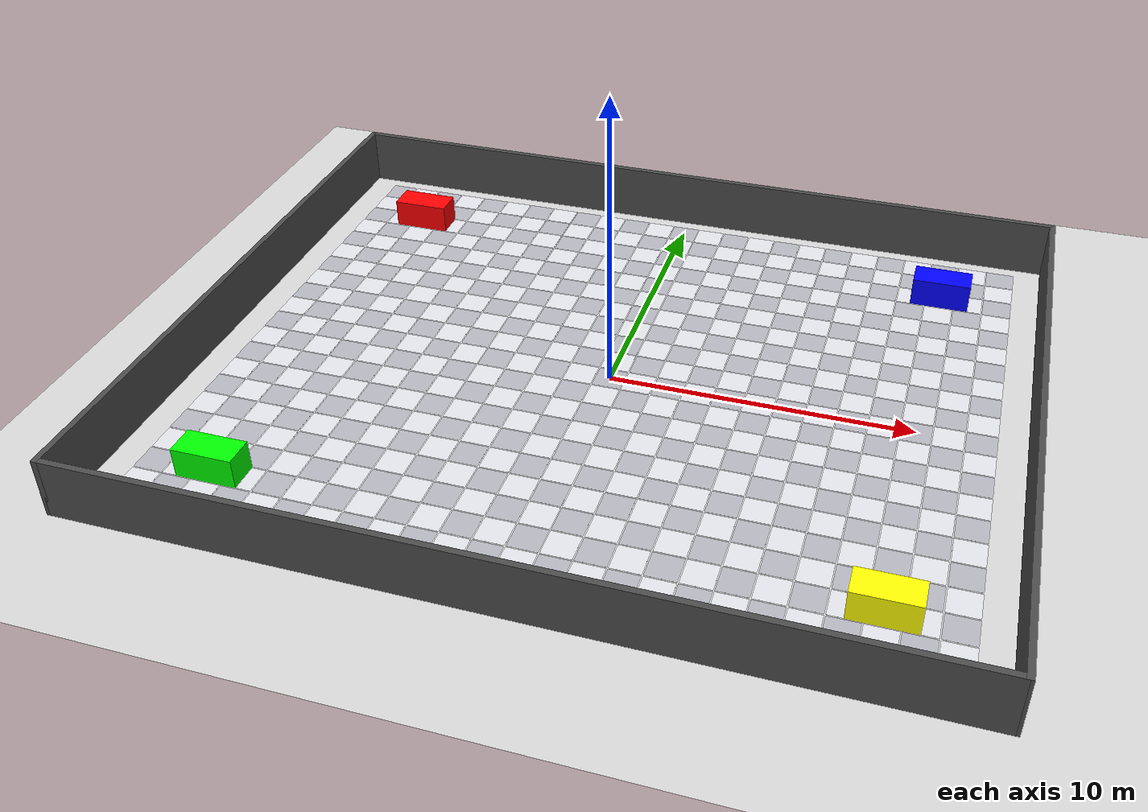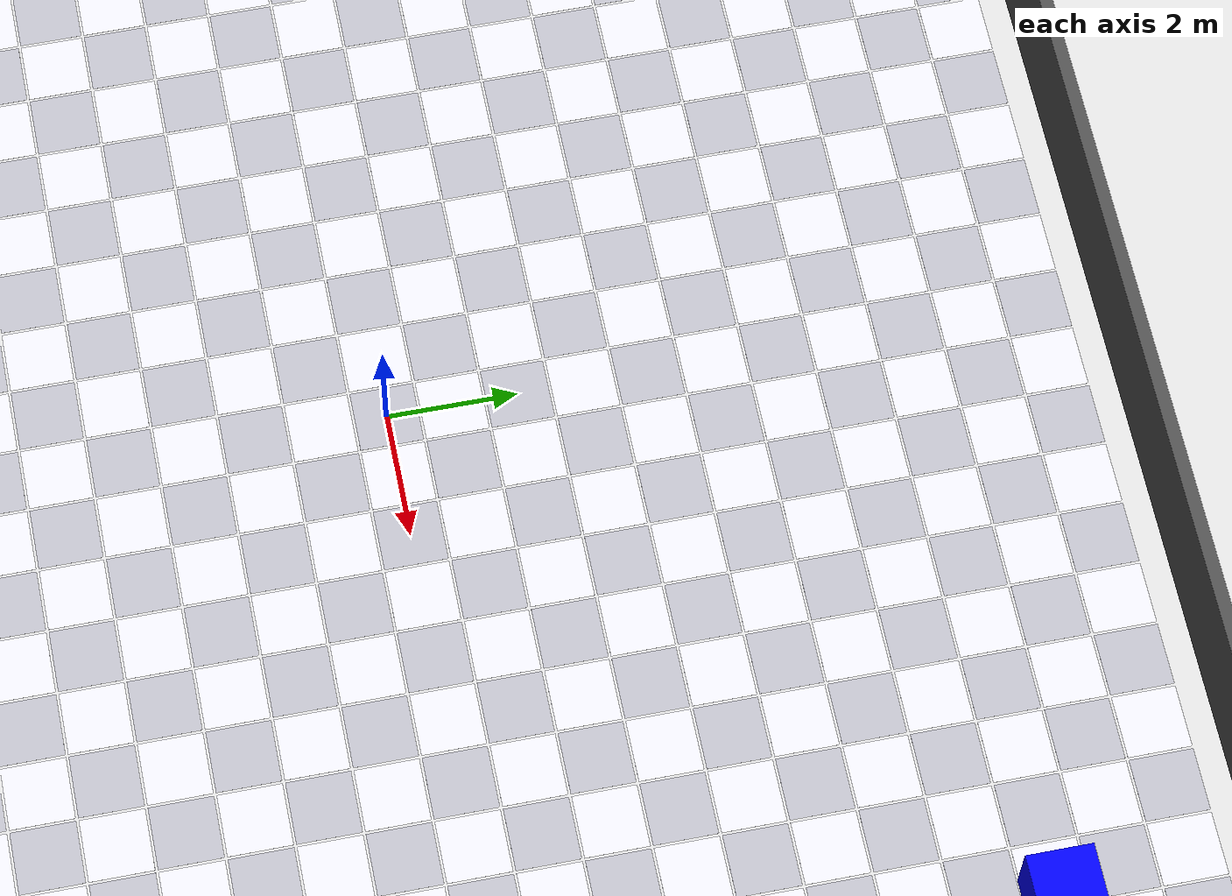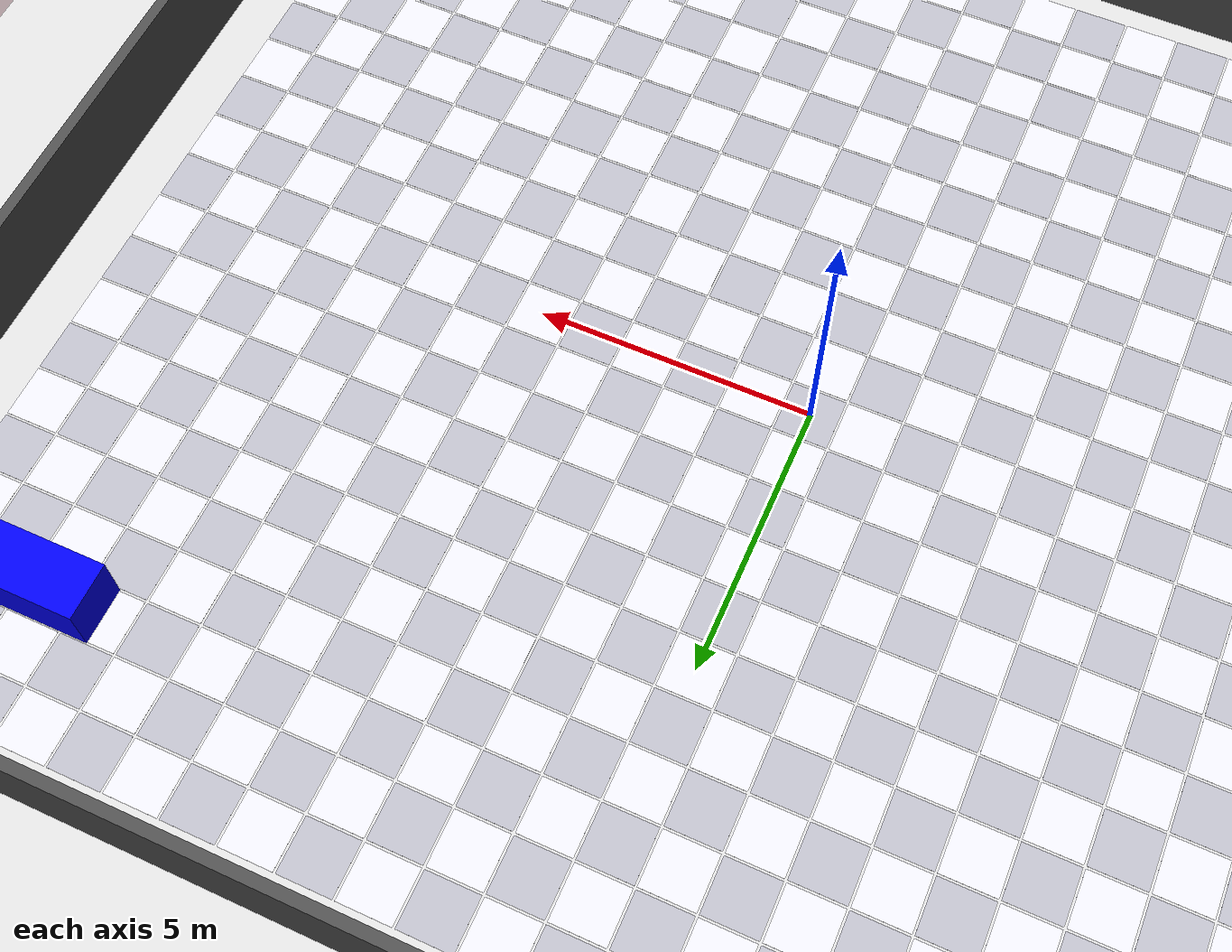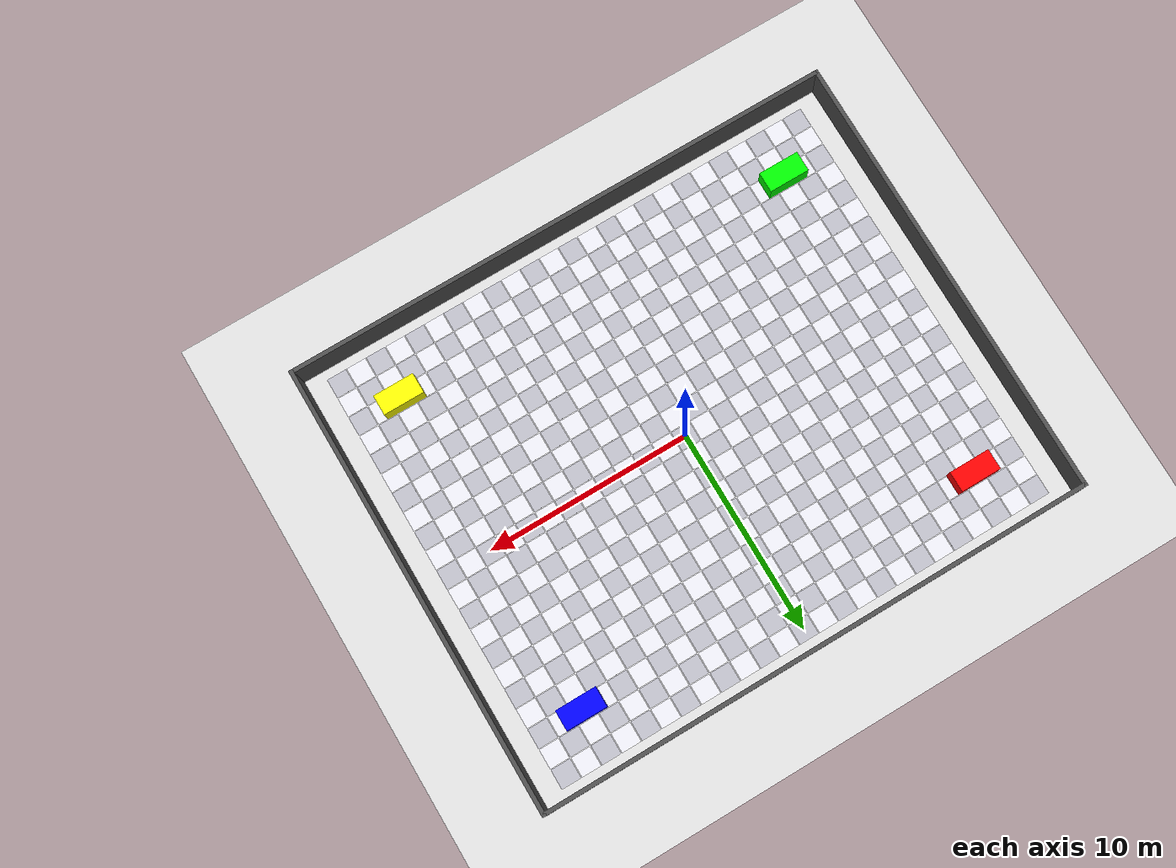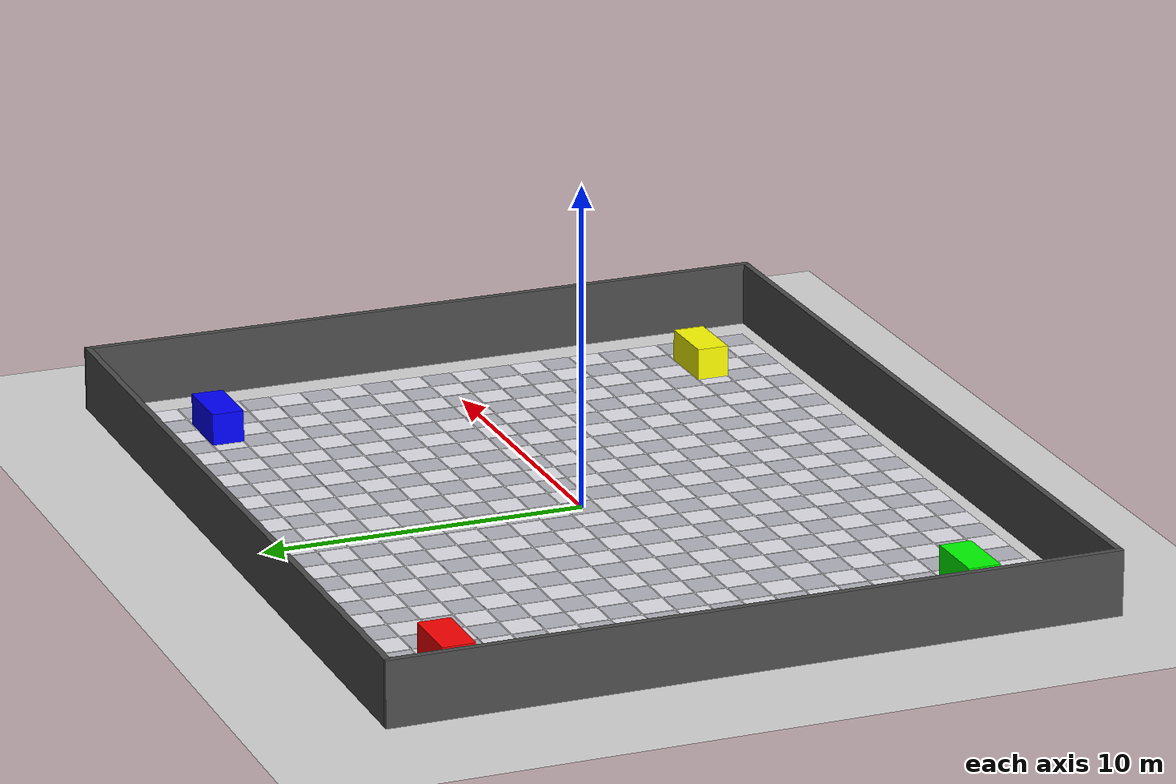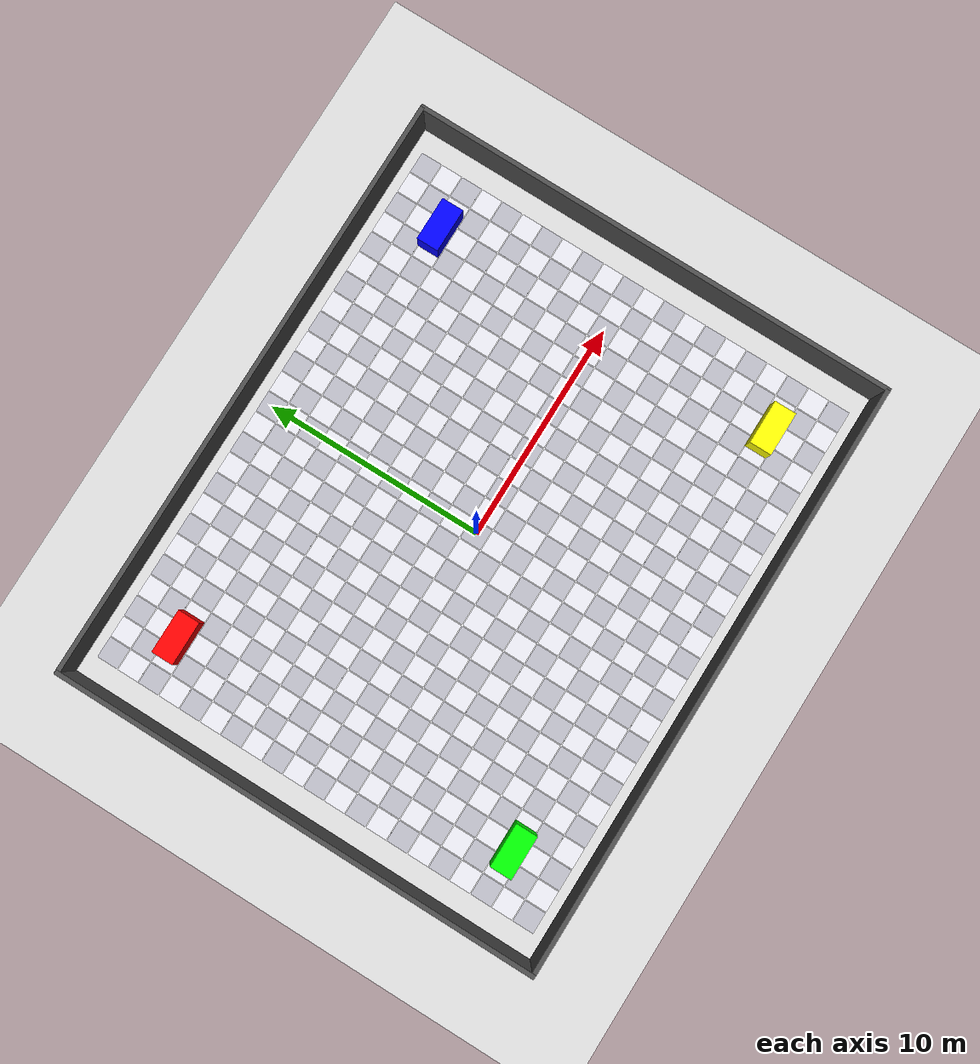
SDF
<?xml version="1.0" ?>
<sdf version="1.7">
  <world name="empty">

    <!-- Core Simulation Plugins -->
    <plugin filename="gz-sim-physics-system" name="gz::sim::systems::Physics"/>
    <plugin filename="gz-sim-user-commands-system" name="gz::sim::systems::UserCommands"/>
    <plugin filename="gz-sim-scene-broadcaster-system" name="gz::sim::systems::SceneBroadcaster"/>
    <plugin filename="gz-sim-contact-system" name="gz::sim::systems::Contact"/>
    <plugin filename="gz-sim-sensors-system" name="gz::sim::systems::Sensors">
      <render_engine>ogre2</render_engine>
    </plugin>
    <plugin filename="gz-sim-imu-system" name="gz::sim::systems::Imu"/>

    <gravity>0 0 -9.8</gravity>
    <scene>
      <ambient>0.6 0.6 0.6 1</ambient>
      <background>0.8 0.85 0.9 1</background>
      <shadows>true</shadows>
    </scene>

    <!-- Sun Light -->
    <include>
      <uri>https://fuel.gazebosim.org/1.0/OpenRobotics/models/Sun</uri>
    </include>

    <!-- Base Floor -->
    <model name="white_floor">
      <static>true</static>
      <pose>0 0 0 0 0 0</pose>
      <link name="floor_link">
        <collision name="collision">
          <geometry><plane><normal>0 0 1</normal><size>35 30</size></plane></geometry>
        </collision>
        <visual name="visual">
          <geometry><plane><normal>0 0 1</normal><size>35 30</size></plane></geometry>
          <material>
            <ambient>0.85 0.85 0.85 1</ambient>
            <diffuse>0.85 0.85 0.85 1</diffuse>
          </material>
        </visual>
      </link>
    </model>

    <!-- High-Contrast Floor Grid for Optical Flow (25m x 21m) -->
    <model name="floor_grid">
      <static>true</static>
      <link name="link">
      <visual name="tile_-12_-10">
        <pose>-12 -10 0.001 0 0 0</pose>
        <geometry><box><size>0.96 0.96 0.002</size></box></geometry>
        <material><ambient>0.72 0.72 0.76 1</ambient><diffuse>0.72 0.72 0.76 1</diffuse></material>
      </visual>
      <visual name="tile_-12_-9">
        <pose>-12 -9 0.001 0 0 0</pose>
        <geometry><box><size>0.96 0.96 0.002</size></box></geometry>
        <material><ambient>0.90 0.90 0.93 1</ambient><diffuse>0.90 0.90 0.93 1</diffuse></material>
      </visual>
      <visual name="tile_-12_-8">
        <pose>-12 -8 0.001 0 0 0</pose>
        <geometry><box><size>0.96 0.96 0.002</size></box></geometry>
        <material><ambient>0.72 0.72 0.76 1</ambient><diffuse>0.72 0.72 0.76 1</diffuse></material>
      </visual>
      <visual name="tile_-12_-7">
        <pose>-12 -7 0.001 0 0 0</pose>
        <geometry><box><size>0.96 0.96 0.002</size></box></geometry>
        <material><ambient>0.90 0.90 0.93 1</ambient><diffuse>0.90 0.90 0.93 1</diffuse></material>
      </visual>
      <visual name="tile_-12_-6">
        <pose>-12 -6 0.001 0 0 0</pose>
        <geometry><box><size>0.96 0.96 0.002</size></box></geometry>
        <material><ambient>0.72 0.72 0.76 1</ambient><diffuse>0.72 0.72 0.76 1</diffuse></material>
      </visual>
      <visual name="tile_-12_-5">
        <pose>-12 -5 0.001 0 0 0</pose>
        <geometry><box><size>0.96 0.96 0.002</size></box></geometry>
        <material><ambient>0.90 0.90 0.93 1</ambient><diffuse>0.90 0.90 0.93 1</diffuse></material>
      </visual>
      <visual name="tile_-12_-4">
        <pose>-12 -4 0.001 0 0 0</pose>
        <geometry><box><size>0.96 0.96 0.002</size></box></geometry>
        <material><ambient>0.72 0.72 0.76 1</ambient><diffuse>0.72 0.72 0.76 1</diffuse></material>
      </visual>
      <visual name="tile_-12_-3">
        <pose>-12 -3 0.001 0 0 0</pose>
        <geometry><box><size>0.96 0.96 0.002</size></box></geometry>
        <material><ambient>0.90 0.90 0.93 1</ambient><diffuse>0.90 0.90 0.93 1</diffuse></material>
      </visual>
      <visual name="tile_-12_-2">
        <pose>-12 -2 0.001 0 0 0</pose>
        <geometry><box><size>0.96 0.96 0.002</size></box></geometry>
        <material><ambient>0.72 0.72 0.76 1</ambient><diffuse>0.72 0.72 0.76 1</diffuse></material>
      </visual>
      <visual name="tile_-12_-1">
        <pose>-12 -1 0.001 0 0 0</pose>
        <geometry><box><size>0.96 0.96 0.002</size></box></geometry>
        <material><ambient>0.90 0.90 0.93 1</ambient><diffuse>0.90 0.90 0.93 1</diffuse></material>
      </visual>
      <visual name="tile_-12_0">
        <pose>-12 0 0.001 0 0 0</pose>
        <geometry><box><size>0.96 0.96 0.002</size></box></geometry>
        <material><ambient>0.72 0.72 0.76 1</ambient><diffuse>0.72 0.72 0.76 1</diffuse></material>
      </visual>
      <visual name="tile_-12_1">
        <pose>-12 1 0.001 0 0 0</pose>
        <geometry><box><size>0.96 0.96 0.002</size></box></geometry>
        <material><ambient>0.90 0.90 0.93 1</ambient><diffuse>0.90 0.90 0.93 1</diffuse></material>
      </visual>
      <visual name="tile_-12_2">
        <pose>-12 2 0.001 0 0 0</pose>
        <geometry><box><size>0.96 0.96 0.002</size></box></geometry>
        <material><ambient>0.72 0.72 0.76 1</ambient><diffuse>0.72 0.72 0.76 1</diffuse></material>
      </visual>
      <visual name="tile_-12_3">
        <pose>-12 3 0.001 0 0 0</pose>
        <geometry><box><size>0.96 0.96 0.002</size></box></geometry>
        <material><ambient>0.90 0.90 0.93 1</ambient><diffuse>0.90 0.90 0.93 1</diffuse></material>
      </visual>
      <visual name="tile_-12_4">
        <pose>-12 4 0.001 0 0 0</pose>
        <geometry><box><size>0.96 0.96 0.002</size></box></geometry>
        <material><ambient>0.72 0.72 0.76 1</ambient><diffuse>0.72 0.72 0.76 1</diffuse></material>
      </visual>
      <visual name="tile_-12_5">
        <pose>-12 5 0.001 0 0 0</pose>
        <geometry><box><size>0.96 0.96 0.002</size></box></geometry>
        <material><ambient>0.90 0.90 0.93 1</ambient><diffuse>0.90 0.90 0.93 1</diffuse></material>
      </visual>
      <visual name="tile_-12_6">
        <pose>-12 6 0.001 0 0 0</pose>
        <geometry><box><size>0.96 0.96 0.002</size></box></geometry>
        <material><ambient>0.72 0.72 0.76 1</ambient><diffuse>0.72 0.72 0.76 1</diffuse></material>
      </visual>
      <visual name="tile_-12_7">
        <pose>-12 7 0.001 0 0 0</pose>
        <geometry><box><size>0.96 0.96 0.002</size></box></geometry>
        <material><ambient>0.90 0.90 0.93 1</ambient><diffuse>0.90 0.90 0.93 1</diffuse></material>
      </visual>
      <visual name="tile_-12_8">
        <pose>-12 8 0.001 0 0 0</pose>
        <geometry><box><size>0.96 0.96 0.002</size></box></geometry>
        <material><ambient>0.72 0.72 0.76 1</ambient><diffuse>0.72 0.72 0.76 1</diffuse></material>
      </visual>
      <visual name="tile_-12_9">
        <pose>-12 9 0.001 0 0 0</pose>
        <geometry><box><size>0.96 0.96 0.002</size></box></geometry>
        <material><ambient>0.90 0.90 0.93 1</ambient><diffuse>0.90 0.90 0.93 1</diffuse></material>
      </visual>
      <visual name="tile_-12_10">
        <pose>-12 10 0.001 0 0 0</pose>
        <geometry><box><size>0.96 0.96 0.002</size></box></geometry>
        <material><ambient>0.72 0.72 0.76 1</ambient><diffuse>0.72 0.72 0.76 1</diffuse></material>
      </visual>
      <visual name="tile_-11_-10">
        <pose>-11 -10 0.001 0 0 0</pose>
        <geometry><box><size>0.96 0.96 0.002</size></box></geometry>
        <material><ambient>0.90 0.90 0.93 1</ambient><diffuse>0.90 0.90 0.93 1</diffuse></material>
      </visual>
      <visual name="tile_-11_-9">
        <pose>-11 -9 0.001 0 0 0</pose>
        <geometry><box><size>0.96 0.96 0.002</size></box></geometry>
        <material><ambient>0.72 0.72 0.76 1</ambient><diffuse>0.72 0.72 0.76 1</diffuse></material>
      </visual>
      <visual name="tile_-11_-8">
        <pose>-11 -8 0.001 0 0 0</pose>
        <geometry><box><size>0.96 0.96 0.002</size></box></geometry>
        <material><ambient>0.90 0.90 0.93 1</ambient><diffuse>0.90 0.90 0.93 1</diffuse></material>
      </visual>
      <visual name="tile_-11_-7">
        <pose>-11 -7 0.001 0 0 0</pose>
        <geometry><box><size>0.96 0.96 0.002</size></box></geometry>
        <material><ambient>0.72 0.72 0.76 1</ambient><diffuse>0.72 0.72 0.76 1</diffuse></material>
      </visual>
      <visual name="tile_-11_-6">
        <pose>-11 -6 0.001 0 0 0</pose>
        <geometry><box><size>0.96 0.96 0.002</size></box></geometry>
        <material><ambient>0.90 0.90 0.93 1</ambient><diffuse>0.90 0.90 0.93 1</diffuse></material>
      </visual>
      <visual name="tile_-11_-5">
        <pose>-11 -5 0.001 0 0 0</pose>
        <geometry><box><size>0.96 0.96 0.002</size></box></geometry>
        <material><ambient>0.72 0.72 0.76 1</ambient><diffuse>0.72 0.72 0.76 1</diffuse></material>
      </visual>
      <visual name="tile_-11_-4">
        <pose>-11 -4 0.001 0 0 0</pose>
        <geometry><box><size>0.96 0.96 0.002</size></box></geometry>
        <material><ambient>0.90 0.90 0.93 1</ambient><diffuse>0.90 0.90 0.93 1</diffuse></material>
      </visual>
      <visual name="tile_-11_-3">
        <pose>-11 -3 0.001 0 0 0</pose>
        <geometry><box><size>0.96 0.96 0.002</size></box></geometry>
        <material><ambient>0.72 0.72 0.76 1</ambient><diffuse>0.72 0.72 0.76 1</diffuse></material>
      </visual>
      <visual name="tile_-11_-2">
        <pose>-11 -2 0.001 0 0 0</pose>
        <geometry><box><size>0.96 0.96 0.002</size></box></geometry>
        <material><ambient>0.90 0.90 0.93 1</ambient><diffuse>0.90 0.90 0.93 1</diffuse></material>
      </visual>
      <visual name="tile_-11_-1">
        <pose>-11 -1 0.001 0 0 0</pose>
        <geometry><box><size>0.96 0.96 0.002</size></box></geometry>
        <material><ambient>0.72 0.72 0.76 1</ambient><diffuse>0.72 0.72 0.76 1</diffuse></material>
      </visual>
      <visual name="tile_-11_0">
        <pose>-11 0 0.001 0 0 0</pose>
        <geometry><box><size>0.96 0.96 0.002</size></box></geometry>
        <material><ambient>0.90 0.90 0.93 1</ambient><diffuse>0.90 0.90 0.93 1</diffuse></material>
      </visual>
      <visual name="tile_-11_1">
        <pose>-11 1 0.001 0 0 0</pose>
        <geometry><box><size>0.96 0.96 0.002</size></box></geometry>
        <material><ambient>0.72 0.72 0.76 1</ambient><diffuse>0.72 0.72 0.76 1</diffuse></material>
      </visual>
      <visual name="tile_-11_2">
        <pose>-11 2 0.001 0 0 0</pose>
        <geometry><box><size>0.96 0.96 0.002</size></box></geometry>
        <material><ambient>0.90 0.90 0.93 1</ambient><diffuse>0.90 0.90 0.93 1</diffuse></material>
      </visual>
      <visual name="tile_-11_3">
        <pose>-11 3 0.001 0 0 0</pose>
        <geometry><box><size>0.96 0.96 0.002</size></box></geometry>
        <material><ambient>0.72 0.72 0.76 1</ambient><diffuse>0.72 0.72 0.76 1</diffuse></material>
      </visual>
      <visual name="tile_-11_4">
        <pose>-11 4 0.001 0 0 0</pose>
        <geometry><box><size>0.96 0.96 0.002</size></box></geometry>
        <material><ambient>0.90 0.90 0.93 1</ambient><diffuse>0.90 0.90 0.93 1</diffuse></material>
      </visual>
      <visual name="tile_-11_5">
        <pose>-11 5 0.001 0 0 0</pose>
        <geometry><box><size>0.96 0.96 0.002</size></box></geometry>
        <material><ambient>0.72 0.72 0.76 1</ambient><diffuse>0.72 0.72 0.76 1</diffuse></material>
      </visual>
      <visual name="tile_-11_6">
        <pose>-11 6 0.001 0 0 0</pose>
        <geometry><box><size>0.96 0.96 0.002</size></box></geometry>
        <material><ambient>0.90 0.90 0.93 1</ambient><diffuse>0.90 0.90 0.93 1</diffuse></material>
      </visual>
      <visual name="tile_-11_7">
        <pose>-11 7 0.001 0 0 0</pose>
        <geometry><box><size>0.96 0.96 0.002</size></box></geometry>
        <material><ambient>0.72 0.72 0.76 1</ambient><diffuse>0.72 0.72 0.76 1</diffuse></material>
      </visual>
      <visual name="tile_-11_8">
        <pose>-11 8 0.001 0 0 0</pose>
        <geometry><box><size>0.96 0.96 0.002</size></box></geometry>
        <material><ambient>0.90 0.90 0.93 1</ambient><diffuse>0.90 0.90 0.93 1</diffuse></material>
      </visual>
      <visual name="tile_-11_9">
        <pose>-11 9 0.001 0 0 0</pose>
        <geometry><box><size>0.96 0.96 0.002</size></box></geometry>
        <material><ambient>0.72 0.72 0.76 1</ambient><diffuse>0.72 0.72 0.76 1</diffuse></material>
      </visual>
      <visual name="tile_-11_10">
        <pose>-11 10 0.001 0 0 0</pose>
        <geometry><box><size>0.96 0.96 0.002</size></box></geometry>
        <material><ambient>0.90 0.90 0.93 1</ambient><diffuse>0.90 0.90 0.93 1</diffuse></material>
      </visual>
      <visual name="tile_-10_-10">
        <pose>-10 -10 0.001 0 0 0</pose>
        <geometry><box><size>0.96 0.96 0.002</size></box></geometry>
        <material><ambient>0.72 0.72 0.76 1</ambient><diffuse>0.72 0.72 0.76 1</diffuse></material>
      </visual>
      <visual name="tile_-10_-9">
        <pose>-10 -9 0.001 0 0 0</pose>
        <geometry><box><size>0.96 0.96 0.002</size></box></geometry>
        <material><ambient>0.90 0.90 0.93 1</ambient><diffuse>0.90 0.90 0.93 1</diffuse></material>
      </visual>
      <visual name="tile_-10_-8">
        <pose>-10 -8 0.001 0 0 0</pose>
        <geometry><box><size>0.96 0.96 0.002</size></box></geometry>
        <material><ambient>0.72 0.72 0.76 1</ambient><diffuse>0.72 0.72 0.76 1</diffuse></material>
      </visual>
      <visual name="tile_-10_-7">
        <pose>-10 -7 0.001 0 0 0</pose>
        <geometry><box><size>0.96 0.96 0.002</size></box></geometry>
        <material><ambient>0.90 0.90 0.93 1</ambient><diffuse>0.90 0.90 0.93 1</diffuse></material>
      </visual>
      <visual name="tile_-10_-6">
        <pose>-10 -6 0.001 0 0 0</pose>
        <geometry><box><size>0.96 0.96 0.002</size></box></geometry>
        <material><ambient>0.72 0.72 0.76 1</ambient><diffuse>0.72 0.72 0.76 1</diffuse></material>
      </visual>
      <visual name="tile_-10_-5">
        <pose>-10 -5 0.001 0 0 0</pose>
        <geometry><box><size>0.96 0.96 0.002</size></box></geometry>
        <material><ambient>0.90 0.90 0.93 1</ambient><diffuse>0.90 0.90 0.93 1</diffuse></material>
      </visual>
      <visual name="tile_-10_-4">
        <pose>-10 -4 0.001 0 0 0</pose>
        <geometry><box><size>0.96 0.96 0.002</size></box></geometry>
        <material><ambient>0.72 0.72 0.76 1</ambient><diffuse>0.72 0.72 0.76 1</diffuse></material>
      </visual>
      <visual name="tile_-10_-3">
        <pose>-10 -3 0.001 0 0 0</pose>
        <geometry><box><size>0.96 0.96 0.002</size></box></geometry>
        <material><ambient>0.90 0.90 0.93 1</ambient><diffuse>0.90 0.90 0.93 1</diffuse></material>
      </visual>
      <visual name="tile_-10_-2">
        <pose>-10 -2 0.001 0 0 0</pose>
        <geometry><box><size>0.96 0.96 0.002</size></box></geometry>
        <material><ambient>0.72 0.72 0.76 1</ambient><diffuse>0.72 0.72 0.76 1</diffuse></material>
      </visual>
      <visual name="tile_-10_-1">
        <pose>-10 -1 0.001 0 0 0</pose>
        <geometry><box><size>0.96 0.96 0.002</size></box></geometry>
        <material><ambient>0.90 0.90 0.93 1</ambient><diffuse>0.90 0.90 0.93 1</diffuse></material>
      </visual>
      <visual name="tile_-10_0">
        <pose>-10 0 0.001 0 0 0</pose>
        <geometry><box><size>0.96 0.96 0.002</size></box></geometry>
        <material><ambient>0.72 0.72 0.76 1</ambient><diffuse>0.72 0.72 0.76 1</diffuse></material>
      </visual>
      <visual name="tile_-10_1">
        <pose>-10 1 0.001 0 0 0</pose>
        <geometry><box><size>0.96 0.96 0.002</size></box></geometry>
        <material><ambient>0.90 0.90 0.93 1</ambient><diffuse>0.90 0.90 0.93 1</diffuse></material>
      </visual>
      <visual name="tile_-10_2">
        <pose>-10 2 0.001 0 0 0</pose>
        <geometry><box><size>0.96 0.96 0.002</size></box></geometry>
        <material><ambient>0.72 0.72 0.76 1</ambient><diffuse>0.72 0.72 0.76 1</diffuse></material>
      </visual>
      <visual name="tile_-10_3">
        <pose>-10 3 0.001 0 0 0</pose>
        <geometry><box><size>0.96 0.96 0.002</size></box></geometry>
        <material><ambient>0.90 0.90 0.93 1</ambient><diffuse>0.90 0.90 0.93 1</diffuse></material>
      </visual>
      <visual name="tile_-10_4">
        <pose>-10 4 0.001 0 0 0</pose>
        <geometry><box><size>0.96 0.96 0.002</size></box></geometry>
        <material><ambient>0.72 0.72 0.76 1</ambient><diffuse>0.72 0.72 0.76 1</diffuse></material>
      </visual>
      <visual name="tile_-10_5">
        <pose>-10 5 0.001 0 0 0</pose>
        <geometry><box><size>0.96 0.96 0.002</size></box></geometry>
        <material><ambient>0.90 0.90 0.93 1</ambient><diffuse>0.90 0.90 0.93 1</diffuse></material>
      </visual>
      <visual name="tile_-10_6">
        <pose>-10 6 0.001 0 0 0</pose>
        <geometry><box><size>0.96 0.96 0.002</size></box></geometry>
        <material><ambient>0.72 0.72 0.76 1</ambient><diffuse>0.72 0.72 0.76 1</diffuse></material>
      </visual>
      <visual name="tile_-10_7">
        <pose>-10 7 0.001 0 0 0</pose>
        <geometry><box><size>0.96 0.96 0.002</size></box></geometry>
        <material><ambient>0.90 0.90 0.93 1</ambient><diffuse>0.90 0.90 0.93 1</diffuse></material>
      </visual>
      <visual name="tile_-10_8">
        <pose>-10 8 0.001 0 0 0</pose>
        <geometry><box><size>0.96 0.96 0.002</size></box></geometry>
        <material><ambient>0.72 0.72 0.76 1</ambient><diffuse>0.72 0.72 0.76 1</diffuse></material>
      </visual>
      <visual name="tile_-10_9">
        <pose>-10 9 0.001 0 0 0</pose>
        <geometry><box><size>0.96 0.96 0.002</size></box></geometry>
        <material><ambient>0.90 0.90 0.93 1</ambient><diffuse>0.90 0.90 0.93 1</diffuse></material>
      </visual>
      <visual name="tile_-10_10">
        <pose>-10 10 0.001 0 0 0</pose>
        <geometry><box><size>0.96 0.96 0.002</size></box></geometry>
        <material><ambient>0.72 0.72 0.76 1</ambient><diffuse>0.72 0.72 0.76 1</diffuse></material>
      </visual>
      <visual name="tile_-9_-10">
        <pose>-9 -10 0.001 0 0 0</pose>
        <geometry><box><size>0.96 0.96 0.002</size></box></geometry>
        <material><ambient>0.90 0.90 0.93 1</ambient><diffuse>0.90 0.90 0.93 1</diffuse></material>
      </visual>
      <visual name="tile_-9_-9">
        <pose>-9 -9 0.001 0 0 0</pose>
        <geometry><box><size>0.96 0.96 0.002</size></box></geometry>
        <material><ambient>0.72 0.72 0.76 1</ambient><diffuse>0.72 0.72 0.76 1</diffuse></material>
      </visual>
      <visual name="tile_-9_-8">
        <pose>-9 -8 0.001 0 0 0</pose>
        <geometry><box><size>0.96 0.96 0.002</size></box></geometry>
        <material><ambient>0.90 0.90 0.93 1</ambient><diffuse>0.90 0.90 0.93 1</diffuse></material>
      </visual>
      <visual name="tile_-9_-7">
        <pose>-9 -7 0.001 0 0 0</pose>
        <geometry><box><size>0.96 0.96 0.002</size></box></geometry>
        <material><ambient>0.72 0.72 0.76 1</ambient><diffuse>0.72 0.72 0.76 1</diffuse></material>
      </visual>
      <visual name="tile_-9_-6">
        <pose>-9 -6 0.001 0 0 0</pose>
        <geometry><box><size>0.96 0.96 0.002</size></box></geometry>
        <material><ambient>0.90 0.90 0.93 1</ambient><diffuse>0.90 0.90 0.93 1</diffuse></material>
      </visual>
      <visual name="tile_-9_-5">
        <pose>-9 -5 0.001 0 0 0</pose>
        <geometry><box><size>0.96 0.96 0.002</size></box></geometry>
        <material><ambient>0.72 0.72 0.76 1</ambient><diffuse>0.72 0.72 0.76 1</diffuse></material>
      </visual>
      <visual name="tile_-9_-4">
        <pose>-9 -4 0.001 0 0 0</pose>
        <geometry><box><size>0.96 0.96 0.002</size></box></geometry>
        <material><ambient>0.90 0.90 0.93 1</ambient><diffuse>0.90 0.90 0.93 1</diffuse></material>
      </visual>
      <visual name="tile_-9_-3">
        <pose>-9 -3 0.001 0 0 0</pose>
        <geometry><box><size>0.96 0.96 0.002</size></box></geometry>
        <material><ambient>0.72 0.72 0.76 1</ambient><diffuse>0.72 0.72 0.76 1</diffuse></material>
      </visual>
      <visual name="tile_-9_-2">
        <pose>-9 -2 0.001 0 0 0</pose>
        <geometry><box><size>0.96 0.96 0.002</size></box></geometry>
        <material><ambient>0.90 0.90 0.93 1</ambient><diffuse>0.90 0.90 0.93 1</diffuse></material>
      </visual>
      <visual name="tile_-9_-1">
        <pose>-9 -1 0.001 0 0 0</pose>
        <geometry><box><size>0.96 0.96 0.002</size></box></geometry>
        <material><ambient>0.72 0.72 0.76 1</ambient><diffuse>0.72 0.72 0.76 1</diffuse></material>
      </visual>
      <visual name="tile_-9_0">
        <pose>-9 0 0.001 0 0 0</pose>
        <geometry><box><size>0.96 0.96 0.002</size></box></geometry>
        <material><ambient>0.90 0.90 0.93 1</ambient><diffuse>0.90 0.90 0.93 1</diffuse></material>
      </visual>
      <visual name="tile_-9_1">
        <pose>-9 1 0.001 0 0 0</pose>
        <geometry><box><size>0.96 0.96 0.002</size></box></geometry>
        <material><ambient>0.72 0.72 0.76 1</ambient><diffuse>0.72 0.72 0.76 1</diffuse></material>
      </visual>
      <visual name="tile_-9_2">
        <pose>-9 2 0.001 0 0 0</pose>
        <geometry><box><size>0.96 0.96 0.002</size></box></geometry>
        <material><ambient>0.90 0.90 0.93 1</ambient><diffuse>0.90 0.90 0.93 1</diffuse></material>
      </visual>
      <visual name="tile_-9_3">
        <pose>-9 3 0.001 0 0 0</pose>
        <geometry><box><size>0.96 0.96 0.002</size></box></geometry>
        <material><ambient>0.72 0.72 0.76 1</ambient><diffuse>0.72 0.72 0.76 1</diffuse></material>
      </visual>
      <visual name="tile_-9_4">
        <pose>-9 4 0.001 0 0 0</pose>
        <geometry><box><size>0.96 0.96 0.002</size></box></geometry>
        <material><ambient>0.90 0.90 0.93 1</ambient><diffuse>0.90 0.90 0.93 1</diffuse></material>
      </visual>
      <visual name="tile_-9_5">
        <pose>-9 5 0.001 0 0 0</pose>
        <geometry><box><size>0.96 0.96 0.002</size></box></geometry>
        <material><ambient>0.72 0.72 0.76 1</ambient><diffuse>0.72 0.72 0.76 1</diffuse></material>
      </visual>
      <visual name="tile_-9_6">
        <pose>-9 6 0.001 0 0 0</pose>
        <geometry><box><size>0.96 0.96 0.002</size></box></geometry>
        <material><ambient>0.90 0.90 0.93 1</ambient><diffuse>0.90 0.90 0.93 1</diffuse></material>
      </visual>
      <visual name="tile_-9_7">
        <pose>-9 7 0.001 0 0 0</pose>
        <geometry><box><size>0.96 0.96 0.002</size></box></geometry>
        <material><ambient>0.72 0.72 0.76 1</ambient><diffuse>0.72 0.72 0.76 1</diffuse></material>
      </visual>
      <visual name="tile_-9_8">
        <pose>-9 8 0.001 0 0 0</pose>
        <geometry><box><size>0.96 0.96 0.002</size></box></geometry>
        <material><ambient>0.90 0.90 0.93 1</ambient><diffuse>0.90 0.90 0.93 1</diffuse></material>
      </visual>
      <visual name="tile_-9_9">
        <pose>-9 9 0.001 0 0 0</pose>
        <geometry><box><size>0.96 0.96 0.002</size></box></geometry>
        <material><ambient>0.72 0.72 0.76 1</ambient><diffuse>0.72 0.72 0.76 1</diffuse></material>
      </visual>
      <visual name="tile_-9_10">
        <pose>-9 10 0.001 0 0 0</pose>
        <geometry><box><size>0.96 0.96 0.002</size></box></geometry>
        <material><ambient>0.90 0.90 0.93 1</ambient><diffuse>0.90 0.90 0.93 1</diffuse></material>
      </visual>
      <visual name="tile_-8_-10">
        <pose>-8 -10 0.001 0 0 0</pose>
        <geometry><box><size>0.96 0.96 0.002</size></box></geometry>
        <material><ambient>0.72 0.72 0.76 1</ambient><diffuse>0.72 0.72 0.76 1</diffuse></material>
      </visual>
      <visual name="tile_-8_-9">
        <pose>-8 -9 0.001 0 0 0</pose>
        <geometry><box><size>0.96 0.96 0.002</size></box></geometry>
        <material><ambient>0.90 0.90 0.93 1</ambient><diffuse>0.90 0.90 0.93 1</diffuse></material>
      </visual>
      <visual name="tile_-8_-8">
        <pose>-8 -8 0.001 0 0 0</pose>
        <geometry><box><size>0.96 0.96 0.002</size></box></geometry>
        <material><ambient>0.72 0.72 0.76 1</ambient><diffuse>0.72 0.72 0.76 1</diffuse></material>
      </visual>
      <visual name="tile_-8_-7">
        <pose>-8 -7 0.001 0 0 0</pose>
        <geometry><box><size>0.96 0.96 0.002</size></box></geometry>
        <material><ambient>0.90 0.90 0.93 1</ambient><diffuse>0.90 0.90 0.93 1</diffuse></material>
      </visual>
      <visual name="tile_-8_-6">
        <pose>-8 -6 0.001 0 0 0</pose>
        <geometry><box><size>0.96 0.96 0.002</size></box></geometry>
        <material><ambient>0.72 0.72 0.76 1</ambient><diffuse>0.72 0.72 0.76 1</diffuse></material>
      </visual>
      <visual name="tile_-8_-5">
        <pose>-8 -5 0.001 0 0 0</pose>
        <geometry><box><size>0.96 0.96 0.002</size></box></geometry>
        <material><ambient>0.90 0.90 0.93 1</ambient><diffuse>0.90 0.90 0.93 1</diffuse></material>
      </visual>
      <visual name="tile_-8_-4">
        <pose>-8 -4 0.001 0 0 0</pose>
        <geometry><box><size>0.96 0.96 0.002</size></box></geometry>
        <material><ambient>0.72 0.72 0.76 1</ambient><diffuse>0.72 0.72 0.76 1</diffuse></material>
      </visual>
      <visual name="tile_-8_-3">
        <pose>-8 -3 0.001 0 0 0</pose>
        <geometry><box><size>0.96 0.96 0.002</size></box></geometry>
        <material><ambient>0.90 0.90 0.93 1</ambient><diffuse>0.90 0.90 0.93 1</diffuse></material>
      </visual>
      <visual name="tile_-8_-2">
        <pose>-8 -2 0.001 0 0 0</pose>
        <geometry><box><size>0.96 0.96 0.002</size></box></geometry>
        <material><ambient>0.72 0.72 0.76 1</ambient><diffuse>0.72 0.72 0.76 1</diffuse></material>
      </visual>
      <visual name="tile_-8_-1">
        <pose>-8 -1 0.001 0 0 0</pose>
        <geometry><box><size>0.96 0.96 0.002</size></box></geometry>
        <material><ambient>0.90 0.90 0.93 1</ambient><diffuse>0.90 0.90 0.93 1</diffuse></material>
      </visual>
      <visual name="tile_-8_0">
        <pose>-8 0 0.001 0 0 0</pose>
        <geometry><box><size>0.96 0.96 0.002</size></box></geometry>
        <material><ambient>0.72 0.72 0.76 1</ambient><diffuse>0.72 0.72 0.76 1</diffuse></material>
      </visual>
      <visual name="tile_-8_1">
        <pose>-8 1 0.001 0 0 0</pose>
        <geometry><box><size>0.96 0.96 0.002</size></box></geometry>
        <material><ambient>0.90 0.90 0.93 1</ambient><diffuse>0.90 0.90 0.93 1</diffuse></material>
      </visual>
      <visual name="tile_-8_2">
        <pose>-8 2 0.001 0 0 0</pose>
        <geometry><box><size>0.96 0.96 0.002</size></box></geometry>
        <material><ambient>0.72 0.72 0.76 1</ambient><diffuse>0.72 0.72 0.76 1</diffuse></material>
      </visual>
      <visual name="tile_-8_3">
        <pose>-8 3 0.001 0 0 0</pose>
        <geometry><box><size>0.96 0.96 0.002</size></box></geometry>
        <material><ambient>0.90 0.90 0.93 1</ambient><diffuse>0.90 0.90 0.93 1</diffuse></material>
      </visual>
      <visual name="tile_-8_4">
        <pose>-8 4 0.001 0 0 0</pose>
        <geometry><box><size>0.96 0.96 0.002</size></box></geometry>
        <material><ambient>0.72 0.72 0.76 1</ambient><diffuse>0.72 0.72 0.76 1</diffuse></material>
      </visual>
      <visual name="tile_-8_5">
        <pose>-8 5 0.001 0 0 0</pose>
        <geometry><box><size>0.96 0.96 0.002</size></box></geometry>
        <material><ambient>0.90 0.90 0.93 1</ambient><diffuse>0.90 0.90 0.93 1</diffuse></material>
      </visual>
      <visual name="tile_-8_6">
        <pose>-8 6 0.001 0 0 0</pose>
        <geometry><box><size>0.96 0.96 0.002</size></box></geometry>
        <material><ambient>0.72 0.72 0.76 1</ambient><diffuse>0.72 0.72 0.76 1</diffuse></material>
      </visual>
      <visual name="tile_-8_7">
        <pose>-8 7 0.001 0 0 0</pose>
        <geometry><box><size>0.96 0.96 0.002</size></box></geometry>
        <material><ambient>0.90 0.90 0.93 1</ambient><diffuse>0.90 0.90 0.93 1</diffuse></material>
      </visual>
      <visual name="tile_-8_8">
        <pose>-8 8 0.001 0 0 0</pose>
        <geometry><box><size>0.96 0.96 0.002</size></box></geometry>
        <material><ambient>0.72 0.72 0.76 1</ambient><diffuse>0.72 0.72 0.76 1</diffuse></material>
      </visual>
      <visual name="tile_-8_9">
        <pose>-8 9 0.001 0 0 0</pose>
        <geometry><box><size>0.96 0.96 0.002</size></box></geometry>
        <material><ambient>0.90 0.90 0.93 1</ambient><diffuse>0.90 0.90 0.93 1</diffuse></material>
      </visual>
      <visual name="tile_-8_10">
        <pose>-8 10 0.001 0 0 0</pose>
        <geometry><box><size>0.96 0.96 0.002</size></box></geometry>
        <material><ambient>0.72 0.72 0.76 1</ambient><diffuse>0.72 0.72 0.76 1</diffuse></material>
      </visual>
      <visual name="tile_-7_-10">
        <pose>-7 -10 0.001 0 0 0</pose>
        <geometry><box><size>0.96 0.96 0.002</size></box></geometry>
        <material><ambient>0.90 0.90 0.93 1</ambient><diffuse>0.90 0.90 0.93 1</diffuse></material>
      </visual>
      <visual name="tile_-7_-9">
        <pose>-7 -9 0.001 0 0 0</pose>
        <geometry><box><size>0.96 0.96 0.002</size></box></geometry>
        <material><ambient>0.72 0.72 0.76 1</ambient><diffuse>0.72 0.72 0.76 1</diffuse></material>
      </visual>
      <visual name="tile_-7_-8">
        <pose>-7 -8 0.001 0 0 0</pose>
        <geometry><box><size>0.96 0.96 0.002</size></box></geometry>
        <material><ambient>0.90 0.90 0.93 1</ambient><diffuse>0.90 0.90 0.93 1</diffuse></material>
      </visual>
      <visual name="tile_-7_-7">
        <pose>-7 -7 0.001 0 0 0</pose>
        <geometry><box><size>0.96 0.96 0.002</size></box></geometry>
        <material><ambient>0.72 0.72 0.76 1</ambient><diffuse>0.72 0.72 0.76 1</diffuse></material>
      </visual>
      <visual name="tile_-7_-6">
        <pose>-7 -6 0.001 0 0 0</pose>
        <geometry><box><size>0.96 0.96 0.002</size></box></geometry>
        <material><ambient>0.90 0.90 0.93 1</ambient><diffuse>0.90 0.90 0.93 1</diffuse></material>
      </visual>
      <visual name="tile_-7_-5">
        <pose>-7 -5 0.001 0 0 0</pose>
        <geometry><box><size>0.96 0.96 0.002</size></box></geometry>
        <material><ambient>0.72 0.72 0.76 1</ambient><diffuse>0.72 0.72 0.76 1</diffuse></material>
      </visual>
      <visual name="tile_-7_-4">
        <pose>-7 -4 0.001 0 0 0</pose>
        <geometry><box><size>0.96 0.96 0.002</size></box></geometry>
        <material><ambient>0.90 0.90 0.93 1</ambient><diffuse>0.90 0.90 0.93 1</diffuse></material>
      </visual>
      <visual name="tile_-7_-3">
        <pose>-7 -3 0.001 0 0 0</pose>
        <geometry><box><size>0.96 0.96 0.002</size></box></geometry>
        <material><ambient>0.72 0.72 0.76 1</ambient><diffuse>0.72 0.72 0.76 1</diffuse></material>
      </visual>
      <visual name="tile_-7_-2">
        <pose>-7 -2 0.001 0 0 0</pose>
        <geometry><box><size>0.96 0.96 0.002</size></box></geometry>
        <material><ambient>0.90 0.90 0.93 1</ambient><diffuse>0.90 0.90 0.93 1</diffuse></material>
      </visual>
      <visual name="tile_-7_-1">
        <pose>-7 -1 0.001 0 0 0</pose>
        <geometry><box><size>0.96 0.96 0.002</size></box></geometry>
        <material><ambient>0.72 0.72 0.76 1</ambient><diffuse>0.72 0.72 0.76 1</diffuse></material>
      </visual>
      <visual name="tile_-7_0">
        <pose>-7 0 0.001 0 0 0</pose>
        <geometry><box><size>0.96 0.96 0.002</size></box></geometry>
        <material><ambient>0.90 0.90 0.93 1</ambient><diffuse>0.90 0.90 0.93 1</diffuse></material>
      </visual>
      <visual name="tile_-7_1">
        <pose>-7 1 0.001 0 0 0</pose>
        <geometry><box><size>0.96 0.96 0.002</size></box></geometry>
        <material><ambient>0.72 0.72 0.76 1</ambient><diffuse>0.72 0.72 0.76 1</diffuse></material>
      </visual>
      <visual name="tile_-7_2">
        <pose>-7 2 0.001 0 0 0</pose>
        <geometry><box><size>0.96 0.96 0.002</size></box></geometry>
        <material><ambient>0.90 0.90 0.93 1</ambient><diffuse>0.90 0.90 0.93 1</diffuse></material>
      </visual>
      <visual name="tile_-7_3">
        <pose>-7 3 0.001 0 0 0</pose>
        <geometry><box><size>0.96 0.96 0.002</size></box></geometry>
        <material><ambient>0.72 0.72 0.76 1</ambient><diffuse>0.72 0.72 0.76 1</diffuse></material>
      </visual>
      <visual name="tile_-7_4">
        <pose>-7 4 0.001 0 0 0</pose>
        <geometry><box><size>0.96 0.96 0.002</size></box></geometry>
        <material><ambient>0.90 0.90 0.93 1</ambient><diffuse>0.90 0.90 0.93 1</diffuse></material>
      </visual>
      <visual name="tile_-7_5">
        <pose>-7 5 0.001 0 0 0</pose>
        <geometry><box><size>0.96 0.96 0.002</size></box></geometry>
        <material><ambient>0.72 0.72 0.76 1</ambient><diffuse>0.72 0.72 0.76 1</diffuse></material>
      </visual>
      <visual name="tile_-7_6">
        <pose>-7 6 0.001 0 0 0</pose>
        <geometry><box><size>0.96 0.96 0.002</size></box></geometry>
        <material><ambient>0.90 0.90 0.93 1</ambient><diffuse>0.90 0.90 0.93 1</diffuse></material>
      </visual>
      <visual name="tile_-7_7">
        <pose>-7 7 0.001 0 0 0</pose>
        <geometry><box><size>0.96 0.96 0.002</size></box></geometry>
        <material><ambient>0.72 0.72 0.76 1</ambient><diffuse>0.72 0.72 0.76 1</diffuse></material>
      </visual>
      <visual name="tile_-7_8">
        <pose>-7 8 0.001 0 0 0</pose>
        <geometry><box><size>0.96 0.96 0.002</size></box></geometry>
        <material><ambient>0.90 0.90 0.93 1</ambient><diffuse>0.90 0.90 0.93 1</diffuse></material>
      </visual>
      <visual name="tile_-7_9">
        <pose>-7 9 0.001 0 0 0</pose>
        <geometry><box><size>0.96 0.96 0.002</size></box></geometry>
        <material><ambient>0.72 0.72 0.76 1</ambient><diffuse>0.72 0.72 0.76 1</diffuse></material>
      </visual>
      <visual name="tile_-7_10">
        <pose>-7 10 0.001 0 0 0</pose>
        <geometry><box><size>0.96 0.96 0.002</size></box></geometry>
        <material><ambient>0.90 0.90 0.93 1</ambient><diffuse>0.90 0.90 0.93 1</diffuse></material>
      </visual>
      <visual name="tile_-6_-10">
        <pose>-6 -10 0.001 0 0 0</pose>
        <geometry><box><size>0.96 0.96 0.002</size></box></geometry>
        <material><ambient>0.72 0.72 0.76 1</ambient><diffuse>0.72 0.72 0.76 1</diffuse></material>
      </visual>
      <visual name="tile_-6_-9">
        <pose>-6 -9 0.001 0 0 0</pose>
        <geometry><box><size>0.96 0.96 0.002</size></box></geometry>
        <material><ambient>0.90 0.90 0.93 1</ambient><diffuse>0.90 0.90 0.93 1</diffuse></material>
      </visual>
      <visual name="tile_-6_-8">
        <pose>-6 -8 0.001 0 0 0</pose>
        <geometry><box><size>0.96 0.96 0.002</size></box></geometry>
        <material><ambient>0.72 0.72 0.76 1</ambient><diffuse>0.72 0.72 0.76 1</diffuse></material>
      </visual>
      <visual name="tile_-6_-7">
        <pose>-6 -7 0.001 0 0 0</pose>
        <geometry><box><size>0.96 0.96 0.002</size></box></geometry>
        <material><ambient>0.90 0.90 0.93 1</ambient><diffuse>0.90 0.90 0.93 1</diffuse></material>
      </visual>
      <visual name="tile_-6_-6">
        <pose>-6 -6 0.001 0 0 0</pose>
        <geometry><box><size>0.96 0.96 0.002</size></box></geometry>
        <material><ambient>0.72 0.72 0.76 1</ambient><diffuse>0.72 0.72 0.76 1</diffuse></material>
      </visual>
      <visual name="tile_-6_-5">
        <pose>-6 -5 0.001 0 0 0</pose>
        <geometry><box><size>0.96 0.96 0.002</size></box></geometry>
        <material><ambient>0.90 0.90 0.93 1</ambient><diffuse>0.90 0.90 0.93 1</diffuse></material>
      </visual>
      <visual name="tile_-6_-4">
        <pose>-6 -4 0.001 0 0 0</pose>
        <geometry><box><size>0.96 0.96 0.002</size></box></geometry>
        <material><ambient>0.72 0.72 0.76 1</ambient><diffuse>0.72 0.72 0.76 1</diffuse></material>
      </visual>
      <visual name="tile_-6_-3">
        <pose>-6 -3 0.001 0 0 0</pose>
        <geometry><box><size>0.96 0.96 0.002</size></box></geometry>
        <material><ambient>0.90 0.90 0.93 1</ambient><diffuse>0.90 0.90 0.93 1</diffuse></material>
      </visual>
      <visual name="tile_-6_-2">
        <pose>-6 -2 0.001 0 0 0</pose>
        <geometry><box><size>0.96 0.96 0.002</size></box></geometry>
        <material><ambient>0.72 0.72 0.76 1</ambient><diffuse>0.72 0.72 0.76 1</diffuse></material>
      </visual>
      <visual name="tile_-6_-1">
        <pose>-6 -1 0.001 0 0 0</pose>
        <geometry><box><size>0.96 0.96 0.002</size></box></geometry>
        <material><ambient>0.90 0.90 0.93 1</ambient><diffuse>0.90 0.90 0.93 1</diffuse></material>
      </visual>
      <visual name="tile_-6_0">
        <pose>-6 0 0.001 0 0 0</pose>
        <geometry><box><size>0.96 0.96 0.002</size></box></geometry>
        <material><ambient>0.72 0.72 0.76 1</ambient><diffuse>0.72 0.72 0.76 1</diffuse></material>
      </visual>
      <visual name="tile_-6_1">
        <pose>-6 1 0.001 0 0 0</pose>
        <geometry><box><size>0.96 0.96 0.002</size></box></geometry>
        <material><ambient>0.90 0.90 0.93 1</ambient><diffuse>0.90 0.90 0.93 1</diffuse></material>
      </visual>
      <visual name="tile_-6_2">
        <pose>-6 2 0.001 0 0 0</pose>
        <geometry><box><size>0.96 0.96 0.002</size></box></geometry>
        <material><ambient>0.72 0.72 0.76 1</ambient><diffuse>0.72 0.72 0.76 1</diffuse></material>
      </visual>
      <visual name="tile_-6_3">
        <pose>-6 3 0.001 0 0 0</pose>
        <geometry><box><size>0.96 0.96 0.002</size></box></geometry>
        <material><ambient>0.90 0.90 0.93 1</ambient><diffuse>0.90 0.90 0.93 1</diffuse></material>
      </visual>
      <visual name="tile_-6_4">
        <pose>-6 4 0.001 0 0 0</pose>
        <geometry><box><size>0.96 0.96 0.002</size></box></geometry>
        <material><ambient>0.72 0.72 0.76 1</ambient><diffuse>0.72 0.72 0.76 1</diffuse></material>
      </visual>
      <visual name="tile_-6_5">
        <pose>-6 5 0.001 0 0 0</pose>
        <geometry><box><size>0.96 0.96 0.002</size></box></geometry>
        <material><ambient>0.90 0.90 0.93 1</ambient><diffuse>0.90 0.90 0.93 1</diffuse></material>
      </visual>
      <visual name="tile_-6_6">
        <pose>-6 6 0.001 0 0 0</pose>
        <geometry><box><size>0.96 0.96 0.002</size></box></geometry>
        <material><ambient>0.72 0.72 0.76 1</ambient><diffuse>0.72 0.72 0.76 1</diffuse></material>
      </visual>
      <visual name="tile_-6_7">
        <pose>-6 7 0.001 0 0 0</pose>
        <geometry><box><size>0.96 0.96 0.002</size></box></geometry>
        <material><ambient>0.90 0.90 0.93 1</ambient><diffuse>0.90 0.90 0.93 1</diffuse></material>
      </visual>
      <visual name="tile_-6_8">
        <pose>-6 8 0.001 0 0 0</pose>
        <geometry><box><size>0.96 0.96 0.002</size></box></geometry>
        <material><ambient>0.72 0.72 0.76 1</ambient><diffuse>0.72 0.72 0.76 1</diffuse></material>
      </visual>
      <visual name="tile_-6_9">
        <pose>-6 9 0.001 0 0 0</pose>
        <geometry><box><size>0.96 0.96 0.002</size></box></geometry>
        <material><ambient>0.90 0.90 0.93 1</ambient><diffuse>0.90 0.90 0.93 1</diffuse></material>
      </visual>
      <visual name="tile_-6_10">
        <pose>-6 10 0.001 0 0 0</pose>
        <geometry><box><size>0.96 0.96 0.002</size></box></geometry>
        <material><ambient>0.72 0.72 0.76 1</ambient><diffuse>0.72 0.72 0.76 1</diffuse></material>
      </visual>
      <visual name="tile_-5_-10">
        <pose>-5 -10 0.001 0 0 0</pose>
        <geometry><box><size>0.96 0.96 0.002</size></box></geometry>
        <material><ambient>0.90 0.90 0.93 1</ambient><diffuse>0.90 0.90 0.93 1</diffuse></material>
      </visual>
      <visual name="tile_-5_-9">
        <pose>-5 -9 0.001 0 0 0</pose>
        <geometry><box><size>0.96 0.96 0.002</size></box></geometry>
        <material><ambient>0.72 0.72 0.76 1</ambient><diffuse>0.72 0.72 0.76 1</diffuse></material>
      </visual>
      <visual name="tile_-5_-8">
        <pose>-5 -8 0.001 0 0 0</pose>
        <geometry><box><size>0.96 0.96 0.002</size></box></geometry>
        <material><ambient>0.90 0.90 0.93 1</ambient><diffuse>0.90 0.90 0.93 1</diffuse></material>
      </visual>
      <visual name="tile_-5_-7">
        <pose>-5 -7 0.001 0 0 0</pose>
        <geometry><box><size>0.96 0.96 0.002</size></box></geometry>
        <material><ambient>0.72 0.72 0.76 1</ambient><diffuse>0.72 0.72 0.76 1</diffuse></material>
      </visual>
      <visual name="tile_-5_-6">
        <pose>-5 -6 0.001 0 0 0</pose>
        <geometry><box><size>0.96 0.96 0.002</size></box></geometry>
        <material><ambient>0.90 0.90 0.93 1</ambient><diffuse>0.90 0.90 0.93 1</diffuse></material>
      </visual>
      <visual name="tile_-5_-5">
        <pose>-5 -5 0.001 0 0 0</pose>
        <geometry><box><size>0.96 0.96 0.002</size></box></geometry>
        <material><ambient>0.72 0.72 0.76 1</ambient><diffuse>0.72 0.72 0.76 1</diffuse></material>
      </visual>
      <visual name="tile_-5_-4">
        <pose>-5 -4 0.001 0 0 0</pose>
        <geometry><box><size>0.96 0.96 0.002</size></box></geometry>
        <material><ambient>0.90 0.90 0.93 1</ambient><diffuse>0.90 0.90 0.93 1</diffuse></material>
      </visual>
      <visual name="tile_-5_-3">
        <pose>-5 -3 0.001 0 0 0</pose>
        <geometry><box><size>0.96 0.96 0.002</size></box></geometry>
        <material><ambient>0.72 0.72 0.76 1</ambient><diffuse>0.72 0.72 0.76 1</diffuse></material>
      </visual>
      <visual name="tile_-5_-2">
        <pose>-5 -2 0.001 0 0 0</pose>
        <geometry><box><size>0.96 0.96 0.002</size></box></geometry>
        <material><ambient>0.90 0.90 0.93 1</ambient><diffuse>0.90 0.90 0.93 1</diffuse></material>
      </visual>
      <visual name="tile_-5_-1">
        <pose>-5 -1 0.001 0 0 0</pose>
        <geometry><box><size>0.96 0.96 0.002</size></box></geometry>
        <material><ambient>0.72 0.72 0.76 1</ambient><diffuse>0.72 0.72 0.76 1</diffuse></material>
      </visual>
      <visual name="tile_-5_0">
        <pose>-5 0 0.001 0 0 0</pose>
        <geometry><box><size>0.96 0.96 0.002</size></box></geometry>
        <material><ambient>0.90 0.90 0.93 1</ambient><diffuse>0.90 0.90 0.93 1</diffuse></material>
      </visual>
      <visual name="tile_-5_1">
        <pose>-5 1 0.001 0 0 0</pose>
        <geometry><box><size>0.96 0.96 0.002</size></box></geometry>
        <material><ambient>0.72 0.72 0.76 1</ambient><diffuse>0.72 0.72 0.76 1</diffuse></material>
      </visual>
      <visual name="tile_-5_2">
        <pose>-5 2 0.001 0 0 0</pose>
        <geometry><box><size>0.96 0.96 0.002</size></box></geometry>
        <material><ambient>0.90 0.90 0.93 1</ambient><diffuse>0.90 0.90 0.93 1</diffuse></material>
      </visual>
      <visual name="tile_-5_3">
        <pose>-5 3 0.001 0 0 0</pose>
        <geometry><box><size>0.96 0.96 0.002</size></box></geometry>
        <material><ambient>0.72 0.72 0.76 1</ambient><diffuse>0.72 0.72 0.76 1</diffuse></material>
      </visual>
      <visual name="tile_-5_4">
        <pose>-5 4 0.001 0 0 0</pose>
        <geometry><box><size>0.96 0.96 0.002</size></box></geometry>
        <material><ambient>0.90 0.90 0.93 1</ambient><diffuse>0.90 0.90 0.93 1</diffuse></material>
      </visual>
      <visual name="tile_-5_5">
        <pose>-5 5 0.001 0 0 0</pose>
        <geometry><box><size>0.96 0.96 0.002</size></box></geometry>
        <material><ambient>0.72 0.72 0.76 1</ambient><diffuse>0.72 0.72 0.76 1</diffuse></material>
      </visual>
      <visual name="tile_-5_6">
        <pose>-5 6 0.001 0 0 0</pose>
        <geometry><box><size>0.96 0.96 0.002</size></box></geometry>
        <material><ambient>0.90 0.90 0.93 1</ambient><diffuse>0.90 0.90 0.93 1</diffuse></material>
      </visual>
      <visual name="tile_-5_7">
        <pose>-5 7 0.001 0 0 0</pose>
        <geometry><box><size>0.96 0.96 0.002</size></box></geometry>
        <material><ambient>0.72 0.72 0.76 1</ambient><diffuse>0.72 0.72 0.76 1</diffuse></material>
      </visual>
      <visual name="tile_-5_8">
        <pose>-5 8 0.001 0 0 0</pose>
        <geometry><box><size>0.96 0.96 0.002</size></box></geometry>
        <material><ambient>0.90 0.90 0.93 1</ambient><diffuse>0.90 0.90 0.93 1</diffuse></material>
      </visual>
      <visual name="tile_-5_9">
        <pose>-5 9 0.001 0 0 0</pose>
        <geometry><box><size>0.96 0.96 0.002</size></box></geometry>
        <material><ambient>0.72 0.72 0.76 1</ambient><diffuse>0.72 0.72 0.76 1</diffuse></material>
      </visual>
      <visual name="tile_-5_10">
        <pose>-5 10 0.001 0 0 0</pose>
        <geometry><box><size>0.96 0.96 0.002</size></box></geometry>
        <material><ambient>0.90 0.90 0.93 1</ambient><diffuse>0.90 0.90 0.93 1</diffuse></material>
      </visual>
      <visual name="tile_-4_-10">
        <pose>-4 -10 0.001 0 0 0</pose>
        <geometry><box><size>0.96 0.96 0.002</size></box></geometry>
        <material><ambient>0.72 0.72 0.76 1</ambient><diffuse>0.72 0.72 0.76 1</diffuse></material>
      </visual>
      <visual name="tile_-4_-9">
        <pose>-4 -9 0.001 0 0 0</pose>
        <geometry><box><size>0.96 0.96 0.002</size></box></geometry>
        <material><ambient>0.90 0.90 0.93 1</ambient><diffuse>0.90 0.90 0.93 1</diffuse></material>
      </visual>
      <visual name="tile_-4_-8">
        <pose>-4 -8 0.001 0 0 0</pose>
        <geometry><box><size>0.96 0.96 0.002</size></box></geometry>
        <material><ambient>0.72 0.72 0.76 1</ambient><diffuse>0.72 0.72 0.76 1</diffuse></material>
      </visual>
      <visual name="tile_-4_-7">
        <pose>-4 -7 0.001 0 0 0</pose>
        <geometry><box><size>0.96 0.96 0.002</size></box></geometry>
        <material><ambient>0.90 0.90 0.93 1</ambient><diffuse>0.90 0.90 0.93 1</diffuse></material>
      </visual>
      <visual name="tile_-4_-6">
        <pose>-4 -6 0.001 0 0 0</pose>
        <geometry><box><size>0.96 0.96 0.002</size></box></geometry>
        <material><ambient>0.72 0.72 0.76 1</ambient><diffuse>0.72 0.72 0.76 1</diffuse></material>
      </visual>
      <visual name="tile_-4_-5">
        <pose>-4 -5 0.001 0 0 0</pose>
        <geometry><box><size>0.96 0.96 0.002</size></box></geometry>
        <material><ambient>0.90 0.90 0.93 1</ambient><diffuse>0.90 0.90 0.93 1</diffuse></material>
      </visual>
      <visual name="tile_-4_-4">
        <pose>-4 -4 0.001 0 0 0</pose>
        <geometry><box><size>0.96 0.96 0.002</size></box></geometry>
        <material><ambient>0.72 0.72 0.76 1</ambient><diffuse>0.72 0.72 0.76 1</diffuse></material>
      </visual>
      <visual name="tile_-4_-3">
        <pose>-4 -3 0.001 0 0 0</pose>
        <geometry><box><size>0.96 0.96 0.002</size></box></geometry>
        <material><ambient>0.90 0.90 0.93 1</ambient><diffuse>0.90 0.90 0.93 1</diffuse></material>
      </visual>
      <visual name="tile_-4_-2">
        <pose>-4 -2 0.001 0 0 0</pose>
        <geometry><box><size>0.96 0.96 0.002</size></box></geometry>
        <material><ambient>0.72 0.72 0.76 1</ambient><diffuse>0.72 0.72 0.76 1</diffuse></material>
      </visual>
      <visual name="tile_-4_-1">
        <pose>-4 -1 0.001 0 0 0</pose>
        <geometry><box><size>0.96 0.96 0.002</size></box></geometry>
        <material><ambient>0.90 0.90 0.93 1</ambient><diffuse>0.90 0.90 0.93 1</diffuse></material>
      </visual>
      <visual name="tile_-4_0">
        <pose>-4 0 0.001 0 0 0</pose>
        <geometry><box><size>0.96 0.96 0.002</size></box></geometry>
        <material><ambient>0.72 0.72 0.76 1</ambient><diffuse>0.72 0.72 0.76 1</diffuse></material>
      </visual>
      <visual name="tile_-4_1">
        <pose>-4 1 0.001 0 0 0</pose>
        <geometry><box><size>0.96 0.96 0.002</size></box></geometry>
        <material><ambient>0.90 0.90 0.93 1</ambient><diffuse>0.90 0.90 0.93 1</diffuse></material>
      </visual>
      <visual name="tile_-4_2">
        <pose>-4 2 0.001 0 0 0</pose>
        <geometry><box><size>0.96 0.96 0.002</size></box></geometry>
        <material><ambient>0.72 0.72 0.76 1</ambient><diffuse>0.72 0.72 0.76 1</diffuse></material>
      </visual>
      <visual name="tile_-4_3">
        <pose>-4 3 0.001 0 0 0</pose>
        <geometry><box><size>0.96 0.96 0.002</size></box></geometry>
        <material><ambient>0.90 0.90 0.93 1</ambient><diffuse>0.90 0.90 0.93 1</diffuse></material>
      </visual>
      <visual name="tile_-4_4">
        <pose>-4 4 0.001 0 0 0</pose>
        <geometry><box><size>0.96 0.96 0.002</size></box></geometry>
        <material><ambient>0.72 0.72 0.76 1</ambient><diffuse>0.72 0.72 0.76 1</diffuse></material>
      </visual>
      <visual name="tile_-4_5">
        <pose>-4 5 0.001 0 0 0</pose>
        <geometry><box><size>0.96 0.96 0.002</size></box></geometry>
        <material><ambient>0.90 0.90 0.93 1</ambient><diffuse>0.90 0.90 0.93 1</diffuse></material>
      </visual>
      <visual name="tile_-4_6">
        <pose>-4 6 0.001 0 0 0</pose>
        <geometry><box><size>0.96 0.96 0.002</size></box></geometry>
        <material><ambient>0.72 0.72 0.76 1</ambient><diffuse>0.72 0.72 0.76 1</diffuse></material>
      </visual>
      <visual name="tile_-4_7">
        <pose>-4 7 0.001 0 0 0</pose>
        <geometry><box><size>0.96 0.96 0.002</size></box></geometry>
        <material><ambient>0.90 0.90 0.93 1</ambient><diffuse>0.90 0.90 0.93 1</diffuse></material>
      </visual>
      <visual name="tile_-4_8">
        <pose>-4 8 0.001 0 0 0</pose>
        <geometry><box><size>0.96 0.96 0.002</size></box></geometry>
        <material><ambient>0.72 0.72 0.76 1</ambient><diffuse>0.72 0.72 0.76 1</diffuse></material>
      </visual>
      <visual name="tile_-4_9">
        <pose>-4 9 0.001 0 0 0</pose>
        <geometry><box><size>0.96 0.96 0.002</size></box></geometry>
        <material><ambient>0.90 0.90 0.93 1</ambient><diffuse>0.90 0.90 0.93 1</diffuse></material>
      </visual>
      <visual name="tile_-4_10">
        <pose>-4 10 0.001 0 0 0</pose>
        <geometry><box><size>0.96 0.96 0.002</size></box></geometry>
        <material><ambient>0.72 0.72 0.76 1</ambient><diffuse>0.72 0.72 0.76 1</diffuse></material>
      </visual>
      <visual name="tile_-3_-10">
        <pose>-3 -10 0.001 0 0 0</pose>
        <geometry><box><size>0.96 0.96 0.002</size></box></geometry>
        <material><ambient>0.90 0.90 0.93 1</ambient><diffuse>0.90 0.90 0.93 1</diffuse></material>
      </visual>
      <visual name="tile_-3_-9">
        <pose>-3 -9 0.001 0 0 0</pose>
        <geometry><box><size>0.96 0.96 0.002</size></box></geometry>
        <material><ambient>0.72 0.72 0.76 1</ambient><diffuse>0.72 0.72 0.76 1</diffuse></material>
      </visual>
      <visual name="tile_-3_-8">
        <pose>-3 -8 0.001 0 0 0</pose>
        <geometry><box><size>0.96 0.96 0.002</size></box></geometry>
        <material><ambient>0.90 0.90 0.93 1</ambient><diffuse>0.90 0.90 0.93 1</diffuse></material>
      </visual>
      <visual name="tile_-3_-7">
        <pose>-3 -7 0.001 0 0 0</pose>
        <geometry><box><size>0.96 0.96 0.002</size></box></geometry>
        <material><ambient>0.72 0.72 0.76 1</ambient><diffuse>0.72 0.72 0.76 1</diffuse></material>
      </visual>
      <visual name="tile_-3_-6">
        <pose>-3 -6 0.001 0 0 0</pose>
        <geometry><box><size>0.96 0.96 0.002</size></box></geometry>
        <material><ambient>0.90 0.90 0.93 1</ambient><diffuse>0.90 0.90 0.93 1</diffuse></material>
      </visual>
      <visual name="tile_-3_-5">
        <pose>-3 -5 0.001 0 0 0</pose>
        <geometry><box><size>0.96 0.96 0.002</size></box></geometry>
        <material><ambient>0.72 0.72 0.76 1</ambient><diffuse>0.72 0.72 0.76 1</diffuse></material>
      </visual>
      <visual name="tile_-3_-4">
        <pose>-3 -4 0.001 0 0 0</pose>
        <geometry><box><size>0.96 0.96 0.002</size></box></geometry>
        <material><ambient>0.90 0.90 0.93 1</ambient><diffuse>0.90 0.90 0.93 1</diffuse></material>
      </visual>
      <visual name="tile_-3_-3">
        <pose>-3 -3 0.001 0 0 0</pose>
        <geometry><box><size>0.96 0.96 0.002</size></box></geometry>
        <material><ambient>0.72 0.72 0.76 1</ambient><diffuse>0.72 0.72 0.76 1</diffuse></material>
      </visual>
      <visual name="tile_-3_-2">
        <pose>-3 -2 0.001 0 0 0</pose>
        <geometry><box><size>0.96 0.96 0.002</size></box></geometry>
        <material><ambient>0.90 0.90 0.93 1</ambient><diffuse>0.90 0.90 0.93 1</diffuse></material>
      </visual>
      <visual name="tile_-3_-1">
        <pose>-3 -1 0.001 0 0 0</pose>
        <geometry><box><size>0.96 0.96 0.002</size></box></geometry>
        <material><ambient>0.72 0.72 0.76 1</ambient><diffuse>0.72 0.72 0.76 1</diffuse></material>
      </visual>
      <visual name="tile_-3_0">
        <pose>-3 0 0.001 0 0 0</pose>
        <geometry><box><size>0.96 0.96 0.002</size></box></geometry>
        <material><ambient>0.90 0.90 0.93 1</ambient><diffuse>0.90 0.90 0.93 1</diffuse></material>
      </visual>
      <visual name="tile_-3_1">
        <pose>-3 1 0.001 0 0 0</pose>
        <geometry><box><size>0.96 0.96 0.002</size></box></geometry>
        <material><ambient>0.72 0.72 0.76 1</ambient><diffuse>0.72 0.72 0.76 1</diffuse></material>
      </visual>
      <visual name="tile_-3_2">
        <pose>-3 2 0.001 0 0 0</pose>
        <geometry><box><size>0.96 0.96 0.002</size></box></geometry>
        <material><ambient>0.90 0.90 0.93 1</ambient><diffuse>0.90 0.90 0.93 1</diffuse></material>
      </visual>
      <visual name="tile_-3_3">
        <pose>-3 3 0.001 0 0 0</pose>
        <geometry><box><size>0.96 0.96 0.002</size></box></geometry>
        <material><ambient>0.72 0.72 0.76 1</ambient><diffuse>0.72 0.72 0.76 1</diffuse></material>
      </visual>
      <visual name="tile_-3_4">
        <pose>-3 4 0.001 0 0 0</pose>
        <geometry><box><size>0.96 0.96 0.002</size></box></geometry>
        <material><ambient>0.90 0.90 0.93 1</ambient><diffuse>0.90 0.90 0.93 1</diffuse></material>
      </visual>
      <visual name="tile_-3_5">
        <pose>-3 5 0.001 0 0 0</pose>
        <geometry><box><size>0.96 0.96 0.002</size></box></geometry>
        <material><ambient>0.72 0.72 0.76 1</ambient><diffuse>0.72 0.72 0.76 1</diffuse></material>
      </visual>
      <visual name="tile_-3_6">
        <pose>-3 6 0.001 0 0 0</pose>
        <geometry><box><size>0.96 0.96 0.002</size></box></geometry>
        <material><ambient>0.90 0.90 0.93 1</ambient><diffuse>0.90 0.90 0.93 1</diffuse></material>
      </visual>
      <visual name="tile_-3_7">
        <pose>-3 7 0.001 0 0 0</pose>
        <geometry><box><size>0.96 0.96 0.002</size></box></geometry>
        <material><ambient>0.72 0.72 0.76 1</ambient><diffuse>0.72 0.72 0.76 1</diffuse></material>
      </visual>
      <visual name="tile_-3_8">
        <pose>-3 8 0.001 0 0 0</pose>
        <geometry><box><size>0.96 0.96 0.002</size></box></geometry>
        <material><ambient>0.90 0.90 0.93 1</ambient><diffuse>0.90 0.90 0.93 1</diffuse></material>
      </visual>
      <visual name="tile_-3_9">
        <pose>-3 9 0.001 0 0 0</pose>
        <geometry><box><size>0.96 0.96 0.002</size></box></geometry>
        <material><ambient>0.72 0.72 0.76 1</ambient><diffuse>0.72 0.72 0.76 1</diffuse></material>
      </visual>
      <visual name="tile_-3_10">
        <pose>-3 10 0.001 0 0 0</pose>
        <geometry><box><size>0.96 0.96 0.002</size></box></geometry>
        <material><ambient>0.90 0.90 0.93 1</ambient><diffuse>0.90 0.90 0.93 1</diffuse></material>
      </visual>
      <visual name="tile_-2_-10">
        <pose>-2 -10 0.001 0 0 0</pose>
        <geometry><box><size>0.96 0.96 0.002</size></box></geometry>
        <material><ambient>0.72 0.72 0.76 1</ambient><diffuse>0.72 0.72 0.76 1</diffuse></material>
      </visual>
      <visual name="tile_-2_-9">
        <pose>-2 -9 0.001 0 0 0</pose>
        <geometry><box><size>0.96 0.96 0.002</size></box></geometry>
        <material><ambient>0.90 0.90 0.93 1</ambient><diffuse>0.90 0.90 0.93 1</diffuse></material>
      </visual>
      <visual name="tile_-2_-8">
        <pose>-2 -8 0.001 0 0 0</pose>
        <geometry><box><size>0.96 0.96 0.002</size></box></geometry>
        <material><ambient>0.72 0.72 0.76 1</ambient><diffuse>0.72 0.72 0.76 1</diffuse></material>
      </visual>
      <visual name="tile_-2_-7">
        <pose>-2 -7 0.001 0 0 0</pose>
        <geometry><box><size>0.96 0.96 0.002</size></box></geometry>
        <material><ambient>0.90 0.90 0.93 1</ambient><diffuse>0.90 0.90 0.93 1</diffuse></material>
      </visual>
      <visual name="tile_-2_-6">
        <pose>-2 -6 0.001 0 0 0</pose>
        <geometry><box><size>0.96 0.96 0.002</size></box></geometry>
        <material><ambient>0.72 0.72 0.76 1</ambient><diffuse>0.72 0.72 0.76 1</diffuse></material>
      </visual>
      <visual name="tile_-2_-5">
        <pose>-2 -5 0.001 0 0 0</pose>
        <geometry><box><size>0.96 0.96 0.002</size></box></geometry>
        <material><ambient>0.90 0.90 0.93 1</ambient><diffuse>0.90 0.90 0.93 1</diffuse></material>
      </visual>
      <visual name="tile_-2_-4">
        <pose>-2 -4 0.001 0 0 0</pose>
        <geometry><box><size>0.96 0.96 0.002</size></box></geometry>
        <material><ambient>0.72 0.72 0.76 1</ambient><diffuse>0.72 0.72 0.76 1</diffuse></material>
      </visual>
      <visual name="tile_-2_-3">
        <pose>-2 -3 0.001 0 0 0</pose>
        <geometry><box><size>0.96 0.96 0.002</size></box></geometry>
        <material><ambient>0.90 0.90 0.93 1</ambient><diffuse>0.90 0.90 0.93 1</diffuse></material>
      </visual>
      <visual name="tile_-2_-2">
        <pose>-2 -2 0.001 0 0 0</pose>
        <geometry><box><size>0.96 0.96 0.002</size></box></geometry>
        <material><ambient>0.72 0.72 0.76 1</ambient><diffuse>0.72 0.72 0.76 1</diffuse></material>
      </visual>
      <visual name="tile_-2_-1">
        <pose>-2 -1 0.001 0 0 0</pose>
        <geometry><box><size>0.96 0.96 0.002</size></box></geometry>
        <material><ambient>0.90 0.90 0.93 1</ambient><diffuse>0.90 0.90 0.93 1</diffuse></material>
      </visual>
      <visual name="tile_-2_0">
        <pose>-2 0 0.001 0 0 0</pose>
        <geometry><box><size>0.96 0.96 0.002</size></box></geometry>
        <material><ambient>0.72 0.72 0.76 1</ambient><diffuse>0.72 0.72 0.76 1</diffuse></material>
      </visual>
      <visual name="tile_-2_1">
        <pose>-2 1 0.001 0 0 0</pose>
        <geometry><box><size>0.96 0.96 0.002</size></box></geometry>
        <material><ambient>0.90 0.90 0.93 1</ambient><diffuse>0.90 0.90 0.93 1</diffuse></material>
      </visual>
      <visual name="tile_-2_2">
        <pose>-2 2 0.001 0 0 0</pose>
        <geometry><box><size>0.96 0.96 0.002</size></box></geometry>
        <material><ambient>0.72 0.72 0.76 1</ambient><diffuse>0.72 0.72 0.76 1</diffuse></material>
      </visual>
      <visual name="tile_-2_3">
        <pose>-2 3 0.001 0 0 0</pose>
        <geometry><box><size>0.96 0.96 0.002</size></box></geometry>
        <material><ambient>0.90 0.90 0.93 1</ambient><diffuse>0.90 0.90 0.93 1</diffuse></material>
      </visual>
      <visual name="tile_-2_4">
        <pose>-2 4 0.001 0 0 0</pose>
        <geometry><box><size>0.96 0.96 0.002</size></box></geometry>
        <material><ambient>0.72 0.72 0.76 1</ambient><diffuse>0.72 0.72 0.76 1</diffuse></material>
      </visual>
      <visual name="tile_-2_5">
        <pose>-2 5 0.001 0 0 0</pose>
        <geometry><box><size>0.96 0.96 0.002</size></box></geometry>
        <material><ambient>0.90 0.90 0.93 1</ambient><diffuse>0.90 0.90 0.93 1</diffuse></material>
      </visual>
      <visual name="tile_-2_6">
        <pose>-2 6 0.001 0 0 0</pose>
        <geometry><box><size>0.96 0.96 0.002</size></box></geometry>
        <material><ambient>0.72 0.72 0.76 1</ambient><diffuse>0.72 0.72 0.76 1</diffuse></material>
      </visual>
      <visual name="tile_-2_7">
        <pose>-2 7 0.001 0 0 0</pose>
        <geometry><box><size>0.96 0.96 0.002</size></box></geometry>
        <material><ambient>0.90 0.90 0.93 1</ambient><diffuse>0.90 0.90 0.93 1</diffuse></material>
      </visual>
      <visual name="tile_-2_8">
        <pose>-2 8 0.001 0 0 0</pose>
        <geometry><box><size>0.96 0.96 0.002</size></box></geometry>
        <material><ambient>0.72 0.72 0.76 1</ambient><diffuse>0.72 0.72 0.76 1</diffuse></material>
      </visual>
      <visual name="tile_-2_9">
        <pose>-2 9 0.001 0 0 0</pose>
        <geometry><box><size>0.96 0.96 0.002</size></box></geometry>
        <material><ambient>0.90 0.90 0.93 1</ambient><diffuse>0.90 0.90 0.93 1</diffuse></material>
      </visual>
      <visual name="tile_-2_10">
        <pose>-2 10 0.001 0 0 0</pose>
        <geometry><box><size>0.96 0.96 0.002</size></box></geometry>
        <material><ambient>0.72 0.72 0.76 1</ambient><diffuse>0.72 0.72 0.76 1</diffuse></material>
      </visual>
      <visual name="tile_-1_-10">
        <pose>-1 -10 0.001 0 0 0</pose>
        <geometry><box><size>0.96 0.96 0.002</size></box></geometry>
        <material><ambient>0.90 0.90 0.93 1</ambient><diffuse>0.90 0.90 0.93 1</diffuse></material>
      </visual>
      <visual name="tile_-1_-9">
        <pose>-1 -9 0.001 0 0 0</pose>
        <geometry><box><size>0.96 0.96 0.002</size></box></geometry>
        <material><ambient>0.72 0.72 0.76 1</ambient><diffuse>0.72 0.72 0.76 1</diffuse></material>
      </visual>
      <visual name="tile_-1_-8">
        <pose>-1 -8 0.001 0 0 0</pose>
        <geometry><box><size>0.96 0.96 0.002</size></box></geometry>
        <material><ambient>0.90 0.90 0.93 1</ambient><diffuse>0.90 0.90 0.93 1</diffuse></material>
      </visual>
      <visual name="tile_-1_-7">
        <pose>-1 -7 0.001 0 0 0</pose>
        <geometry><box><size>0.96 0.96 0.002</size></box></geometry>
        <material><ambient>0.72 0.72 0.76 1</ambient><diffuse>0.72 0.72 0.76 1</diffuse></material>
      </visual>
      <visual name="tile_-1_-6">
        <pose>-1 -6 0.001 0 0 0</pose>
        <geometry><box><size>0.96 0.96 0.002</size></box></geometry>
        <material><ambient>0.90 0.90 0.93 1</ambient><diffuse>0.90 0.90 0.93 1</diffuse></material>
      </visual>
      <visual name="tile_-1_-5">
        <pose>-1 -5 0.001 0 0 0</pose>
        <geometry><box><size>0.96 0.96 0.002</size></box></geometry>
        <material><ambient>0.72 0.72 0.76 1</ambient><diffuse>0.72 0.72 0.76 1</diffuse></material>
      </visual>
      <visual name="tile_-1_-4">
        <pose>-1 -4 0.001 0 0 0</pose>
        <geometry><box><size>0.96 0.96 0.002</size></box></geometry>
        <material><ambient>0.90 0.90 0.93 1</ambient><diffuse>0.90 0.90 0.93 1</diffuse></material>
      </visual>
      <visual name="tile_-1_-3">
        <pose>-1 -3 0.001 0 0 0</pose>
        <geometry><box><size>0.96 0.96 0.002</size></box></geometry>
        <material><ambient>0.72 0.72 0.76 1</ambient><diffuse>0.72 0.72 0.76 1</diffuse></material>
      </visual>
      <visual name="tile_-1_-2">
        <pose>-1 -2 0.001 0 0 0</pose>
        <geometry><box><size>0.96 0.96 0.002</size></box></geometry>
        <material><ambient>0.90 0.90 0.93 1</ambient><diffuse>0.90 0.90 0.93 1</diffuse></material>
      </visual>
      <visual name="tile_-1_-1">
        <pose>-1 -1 0.001 0 0 0</pose>
        <geometry><box><size>0.96 0.96 0.002</size></box></geometry>
        <material><ambient>0.72 0.72 0.76 1</ambient><diffuse>0.72 0.72 0.76 1</diffuse></material>
      </visual>
      <visual name="tile_-1_0">
        <pose>-1 0 0.001 0 0 0</pose>
        <geometry><box><size>0.96 0.96 0.002</size></box></geometry>
        <material><ambient>0.90 0.90 0.93 1</ambient><diffuse>0.90 0.90 0.93 1</diffuse></material>
      </visual>
      <visual name="tile_-1_1">
        <pose>-1 1 0.001 0 0 0</pose>
        <geometry><box><size>0.96 0.96 0.002</size></box></geometry>
        <material><ambient>0.72 0.72 0.76 1</ambient><diffuse>0.72 0.72 0.76 1</diffuse></material>
      </visual>
      <visual name="tile_-1_2">
        <pose>-1 2 0.001 0 0 0</pose>
        <geometry><box><size>0.96 0.96 0.002</size></box></geometry>
        <material><ambient>0.90 0.90 0.93 1</ambient><diffuse>0.90 0.90 0.93 1</diffuse></material>
      </visual>
      <visual name="tile_-1_3">
        <pose>-1 3 0.001 0 0 0</pose>
        <geometry><box><size>0.96 0.96 0.002</size></box></geometry>
        <material><ambient>0.72 0.72 0.76 1</ambient><diffuse>0.72 0.72 0.76 1</diffuse></material>
      </visual>
      <visual name="tile_-1_4">
        <pose>-1 4 0.001 0 0 0</pose>
        <geometry><box><size>0.96 0.96 0.002</size></box></geometry>
        <material><ambient>0.90 0.90 0.93 1</ambient><diffuse>0.90 0.90 0.93 1</diffuse></material>
      </visual>
      <visual name="tile_-1_5">
        <pose>-1 5 0.001 0 0 0</pose>
        <geometry><box><size>0.96 0.96 0.002</size></box></geometry>
        <material><ambient>0.72 0.72 0.76 1</ambient><diffuse>0.72 0.72 0.76 1</diffuse></material>
      </visual>
      <visual name="tile_-1_6">
        <pose>-1 6 0.001 0 0 0</pose>
        <geometry><box><size>0.96 0.96 0.002</size></box></geometry>
        <material><ambient>0.90 0.90 0.93 1</ambient><diffuse>0.90 0.90 0.93 1</diffuse></material>
      </visual>
      <visual name="tile_-1_7">
        <pose>-1 7 0.001 0 0 0</pose>
        <geometry><box><size>0.96 0.96 0.002</size></box></geometry>
        <material><ambient>0.72 0.72 0.76 1</ambient><diffuse>0.72 0.72 0.76 1</diffuse></material>
      </visual>
      <visual name="tile_-1_8">
        <pose>-1 8 0.001 0 0 0</pose>
        <geometry><box><size>0.96 0.96 0.002</size></box></geometry>
        <material><ambient>0.90 0.90 0.93 1</ambient><diffuse>0.90 0.90 0.93 1</diffuse></material>
      </visual>
      <visual name="tile_-1_9">
        <pose>-1 9 0.001 0 0 0</pose>
        <geometry><box><size>0.96 0.96 0.002</size></box></geometry>
        <material><ambient>0.72 0.72 0.76 1</ambient><diffuse>0.72 0.72 0.76 1</diffuse></material>
      </visual>
      <visual name="tile_-1_10">
        <pose>-1 10 0.001 0 0 0</pose>
        <geometry><box><size>0.96 0.96 0.002</size></box></geometry>
        <material><ambient>0.90 0.90 0.93 1</ambient><diffuse>0.90 0.90 0.93 1</diffuse></material>
      </visual>
      <visual name="tile_0_-10">
        <pose>0 -10 0.001 0 0 0</pose>
        <geometry><box><size>0.96 0.96 0.002</size></box></geometry>
        <material><ambient>0.72 0.72 0.76 1</ambient><diffuse>0.72 0.72 0.76 1</diffuse></material>
      </visual>
      <visual name="tile_0_-9">
        <pose>0 -9 0.001 0 0 0</pose>
        <geometry><box><size>0.96 0.96 0.002</size></box></geometry>
        <material><ambient>0.90 0.90 0.93 1</ambient><diffuse>0.90 0.90 0.93 1</diffuse></material>
      </visual>
      <visual name="tile_0_-8">
        <pose>0 -8 0.001 0 0 0</pose>
        <geometry><box><size>0.96 0.96 0.002</size></box></geometry>
        <material><ambient>0.72 0.72 0.76 1</ambient><diffuse>0.72 0.72 0.76 1</diffuse></material>
      </visual>
      <visual name="tile_0_-7">
        <pose>0 -7 0.001 0 0 0</pose>
        <geometry><box><size>0.96 0.96 0.002</size></box></geometry>
        <material><ambient>0.90 0.90 0.93 1</ambient><diffuse>0.90 0.90 0.93 1</diffuse></material>
      </visual>
      <visual name="tile_0_-6">
        <pose>0 -6 0.001 0 0 0</pose>
        <geometry><box><size>0.96 0.96 0.002</size></box></geometry>
        <material><ambient>0.72 0.72 0.76 1</ambient><diffuse>0.72 0.72 0.76 1</diffuse></material>
      </visual>
      <visual name="tile_0_-5">
        <pose>0 -5 0.001 0 0 0</pose>
        <geometry><box><size>0.96 0.96 0.002</size></box></geometry>
        <material><ambient>0.90 0.90 0.93 1</ambient><diffuse>0.90 0.90 0.93 1</diffuse></material>
      </visual>
      <visual name="tile_0_-4">
        <pose>0 -4 0.001 0 0 0</pose>
        <geometry><box><size>0.96 0.96 0.002</size></box></geometry>
        <material><ambient>0.72 0.72 0.76 1</ambient><diffuse>0.72 0.72 0.76 1</diffuse></material>
      </visual>
      <visual name="tile_0_-3">
        <pose>0 -3 0.001 0 0 0</pose>
        <geometry><box><size>0.96 0.96 0.002</size></box></geometry>
        <material><ambient>0.90 0.90 0.93 1</ambient><diffuse>0.90 0.90 0.93 1</diffuse></material>
      </visual>
      <visual name="tile_0_-2">
        <pose>0 -2 0.001 0 0 0</pose>
        <geometry><box><size>0.96 0.96 0.002</size></box></geometry>
        <material><ambient>0.72 0.72 0.76 1</ambient><diffuse>0.72 0.72 0.76 1</diffuse></material>
      </visual>
      <visual name="tile_0_-1">
        <pose>0 -1 0.001 0 0 0</pose>
        <geometry><box><size>0.96 0.96 0.002</size></box></geometry>
        <material><ambient>0.90 0.90 0.93 1</ambient><diffuse>0.90 0.90 0.93 1</diffuse></material>
      </visual>
      <visual name="tile_0_0">
        <pose>0 0 0.001 0 0 0</pose>
        <geometry><box><size>0.96 0.96 0.002</size></box></geometry>
        <material><ambient>0.72 0.72 0.76 1</ambient><diffuse>0.72 0.72 0.76 1</diffuse></material>
      </visual>
      <visual name="tile_0_1">
        <pose>0 1 0.001 0 0 0</pose>
        <geometry><box><size>0.96 0.96 0.002</size></box></geometry>
        <material><ambient>0.90 0.90 0.93 1</ambient><diffuse>0.90 0.90 0.93 1</diffuse></material>
      </visual>
      <visual name="tile_0_2">
        <pose>0 2 0.001 0 0 0</pose>
        <geometry><box><size>0.96 0.96 0.002</size></box></geometry>
        <material><ambient>0.72 0.72 0.76 1</ambient><diffuse>0.72 0.72 0.76 1</diffuse></material>
      </visual>
      <visual name="tile_0_3">
        <pose>0 3 0.001 0 0 0</pose>
        <geometry><box><size>0.96 0.96 0.002</size></box></geometry>
        <material><ambient>0.90 0.90 0.93 1</ambient><diffuse>0.90 0.90 0.93 1</diffuse></material>
      </visual>
      <visual name="tile_0_4">
        <pose>0 4 0.001 0 0 0</pose>
        <geometry><box><size>0.96 0.96 0.002</size></box></geometry>
        <material><ambient>0.72 0.72 0.76 1</ambient><diffuse>0.72 0.72 0.76 1</diffuse></material>
      </visual>
      <visual name="tile_0_5">
        <pose>0 5 0.001 0 0 0</pose>
        <geometry><box><size>0.96 0.96 0.002</size></box></geometry>
        <material><ambient>0.90 0.90 0.93 1</ambient><diffuse>0.90 0.90 0.93 1</diffuse></material>
      </visual>
      <visual name="tile_0_6">
        <pose>0 6 0.001 0 0 0</pose>
        <geometry><box><size>0.96 0.96 0.002</size></box></geometry>
        <material><ambient>0.72 0.72 0.76 1</ambient><diffuse>0.72 0.72 0.76 1</diffuse></material>
      </visual>
      <visual name="tile_0_7">
        <pose>0 7 0.001 0 0 0</pose>
        <geometry><box><size>0.96 0.96 0.002</size></box></geometry>
        <material><ambient>0.90 0.90 0.93 1</ambient><diffuse>0.90 0.90 0.93 1</diffuse></material>
      </visual>
      <visual name="tile_0_8">
        <pose>0 8 0.001 0 0 0</pose>
        <geometry><box><size>0.96 0.96 0.002</size></box></geometry>
        <material><ambient>0.72 0.72 0.76 1</ambient><diffuse>0.72 0.72 0.76 1</diffuse></material>
      </visual>
      <visual name="tile_0_9">
        <pose>0 9 0.001 0 0 0</pose>
        <geometry><box><size>0.96 0.96 0.002</size></box></geometry>
        <material><ambient>0.90 0.90 0.93 1</ambient><diffuse>0.90 0.90 0.93 1</diffuse></material>
      </visual>
      <visual name="tile_0_10">
        <pose>0 10 0.001 0 0 0</pose>
        <geometry><box><size>0.96 0.96 0.002</size></box></geometry>
        <material><ambient>0.72 0.72 0.76 1</ambient><diffuse>0.72 0.72 0.76 1</diffuse></material>
      </visual>
      <visual name="tile_1_-10">
        <pose>1 -10 0.001 0 0 0</pose>
        <geometry><box><size>0.96 0.96 0.002</size></box></geometry>
        <material><ambient>0.90 0.90 0.93 1</ambient><diffuse>0.90 0.90 0.93 1</diffuse></material>
      </visual>
      <visual name="tile_1_-9">
        <pose>1 -9 0.001 0 0 0</pose>
        <geometry><box><size>0.96 0.96 0.002</size></box></geometry>
        <material><ambient>0.72 0.72 0.76 1</ambient><diffuse>0.72 0.72 0.76 1</diffuse></material>
      </visual>
      <visual name="tile_1_-8">
        <pose>1 -8 0.001 0 0 0</pose>
        <geometry><box><size>0.96 0.96 0.002</size></box></geometry>
        <material><ambient>0.90 0.90 0.93 1</ambient><diffuse>0.90 0.90 0.93 1</diffuse></material>
      </visual>
      <visual name="tile_1_-7">
        <pose>1 -7 0.001 0 0 0</pose>
        <geometry><box><size>0.96 0.96 0.002</size></box></geometry>
        <material><ambient>0.72 0.72 0.76 1</ambient><diffuse>0.72 0.72 0.76 1</diffuse></material>
      </visual>
      <visual name="tile_1_-6">
        <pose>1 -6 0.001 0 0 0</pose>
        <geometry><box><size>0.96 0.96 0.002</size></box></geometry>
        <material><ambient>0.90 0.90 0.93 1</ambient><diffuse>0.90 0.90 0.93 1</diffuse></material>
      </visual>
      <visual name="tile_1_-5">
        <pose>1 -5 0.001 0 0 0</pose>
        <geometry><box><size>0.96 0.96 0.002</size></box></geometry>
        <material><ambient>0.72 0.72 0.76 1</ambient><diffuse>0.72 0.72 0.76 1</diffuse></material>
      </visual>
      <visual name="tile_1_-4">
        <pose>1 -4 0.001 0 0 0</pose>
        <geometry><box><size>0.96 0.96 0.002</size></box></geometry>
        <material><ambient>0.90 0.90 0.93 1</ambient><diffuse>0.90 0.90 0.93 1</diffuse></material>
      </visual>
      <visual name="tile_1_-3">
        <pose>1 -3 0.001 0 0 0</pose>
        <geometry><box><size>0.96 0.96 0.002</size></box></geometry>
        <material><ambient>0.72 0.72 0.76 1</ambient><diffuse>0.72 0.72 0.76 1</diffuse></material>
      </visual>
      <visual name="tile_1_-2">
        <pose>1 -2 0.001 0 0 0</pose>
        <geometry><box><size>0.96 0.96 0.002</size></box></geometry>
        <material><ambient>0.90 0.90 0.93 1</ambient><diffuse>0.90 0.90 0.93 1</diffuse></material>
      </visual>
      <visual name="tile_1_-1">
        <pose>1 -1 0.001 0 0 0</pose>
        <geometry><box><size>0.96 0.96 0.002</size></box></geometry>
        <material><ambient>0.72 0.72 0.76 1</ambient><diffuse>0.72 0.72 0.76 1</diffuse></material>
      </visual>
      <visual name="tile_1_0">
        <pose>1 0 0.001 0 0 0</pose>
        <geometry><box><size>0.96 0.96 0.002</size></box></geometry>
        <material><ambient>0.90 0.90 0.93 1</ambient><diffuse>0.90 0.90 0.93 1</diffuse></material>
      </visual>
      <visual name="tile_1_1">
        <pose>1 1 0.001 0 0 0</pose>
        <geometry><box><size>0.96 0.96 0.002</size></box></geometry>
        <material><ambient>0.72 0.72 0.76 1</ambient><diffuse>0.72 0.72 0.76 1</diffuse></material>
      </visual>
      <visual name="tile_1_2">
        <pose>1 2 0.001 0 0 0</pose>
        <geometry><box><size>0.96 0.96 0.002</size></box></geometry>
        <material><ambient>0.90 0.90 0.93 1</ambient><diffuse>0.90 0.90 0.93 1</diffuse></material>
      </visual>
      <visual name="tile_1_3">
        <pose>1 3 0.001 0 0 0</pose>
        <geometry><box><size>0.96 0.96 0.002</size></box></geometry>
        <material><ambient>0.72 0.72 0.76 1</ambient><diffuse>0.72 0.72 0.76 1</diffuse></material>
      </visual>
      <visual name="tile_1_4">
        <pose>1 4 0.001 0 0 0</pose>
        <geometry><box><size>0.96 0.96 0.002</size></box></geometry>
        <material><ambient>0.90 0.90 0.93 1</ambient><diffuse>0.90 0.90 0.93 1</diffuse></material>
      </visual>
      <visual name="tile_1_5">
        <pose>1 5 0.001 0 0 0</pose>
        <geometry><box><size>0.96 0.96 0.002</size></box></geometry>
        <material><ambient>0.72 0.72 0.76 1</ambient><diffuse>0.72 0.72 0.76 1</diffuse></material>
      </visual>
      <visual name="tile_1_6">
        <pose>1 6 0.001 0 0 0</pose>
        <geometry><box><size>0.96 0.96 0.002</size></box></geometry>
        <material><ambient>0.90 0.90 0.93 1</ambient><diffuse>0.90 0.90 0.93 1</diffuse></material>
      </visual>
      <visual name="tile_1_7">
        <pose>1 7 0.001 0 0 0</pose>
        <geometry><box><size>0.96 0.96 0.002</size></box></geometry>
        <material><ambient>0.72 0.72 0.76 1</ambient><diffuse>0.72 0.72 0.76 1</diffuse></material>
      </visual>
      <visual name="tile_1_8">
        <pose>1 8 0.001 0 0 0</pose>
        <geometry><box><size>0.96 0.96 0.002</size></box></geometry>
        <material><ambient>0.90 0.90 0.93 1</ambient><diffuse>0.90 0.90 0.93 1</diffuse></material>
      </visual>
      <visual name="tile_1_9">
        <pose>1 9 0.001 0 0 0</pose>
        <geometry><box><size>0.96 0.96 0.002</size></box></geometry>
        <material><ambient>0.72 0.72 0.76 1</ambient><diffuse>0.72 0.72 0.76 1</diffuse></material>
      </visual>
      <visual name="tile_1_10">
        <pose>1 10 0.001 0 0 0</pose>
        <geometry><box><size>0.96 0.96 0.002</size></box></geometry>
        <material><ambient>0.90 0.90 0.93 1</ambient><diffuse>0.90 0.90 0.93 1</diffuse></material>
      </visual>
      <visual name="tile_2_-10">
        <pose>2 -10 0.001 0 0 0</pose>
        <geometry><box><size>0.96 0.96 0.002</size></box></geometry>
        <material><ambient>0.72 0.72 0.76 1</ambient><diffuse>0.72 0.72 0.76 1</diffuse></material>
      </visual>
      <visual name="tile_2_-9">
        <pose>2 -9 0.001 0 0 0</pose>
        <geometry><box><size>0.96 0.96 0.002</size></box></geometry>
        <material><ambient>0.90 0.90 0.93 1</ambient><diffuse>0.90 0.90 0.93 1</diffuse></material>
      </visual>
      <visual name="tile_2_-8">
        <pose>2 -8 0.001 0 0 0</pose>
        <geometry><box><size>0.96 0.96 0.002</size></box></geometry>
        <material><ambient>0.72 0.72 0.76 1</ambient><diffuse>0.72 0.72 0.76 1</diffuse></material>
      </visual>
      <visual name="tile_2_-7">
        <pose>2 -7 0.001 0 0 0</pose>
        <geometry><box><size>0.96 0.96 0.002</size></box></geometry>
        <material><ambient>0.90 0.90 0.93 1</ambient><diffuse>0.90 0.90 0.93 1</diffuse></material>
      </visual>
      <visual name="tile_2_-6">
        <pose>2 -6 0.001 0 0 0</pose>
        <geometry><box><size>0.96 0.96 0.002</size></box></geometry>
        <material><ambient>0.72 0.72 0.76 1</ambient><diffuse>0.72 0.72 0.76 1</diffuse></material>
      </visual>
      <visual name="tile_2_-5">
        <pose>2 -5 0.001 0 0 0</pose>
        <geometry><box><size>0.96 0.96 0.002</size></box></geometry>
        <material><ambient>0.90 0.90 0.93 1</ambient><diffuse>0.90 0.90 0.93 1</diffuse></material>
      </visual>
      <visual name="tile_2_-4">
        <pose>2 -4 0.001 0 0 0</pose>
        <geometry><box><size>0.96 0.96 0.002</size></box></geometry>
        <material><ambient>0.72 0.72 0.76 1</ambient><diffuse>0.72 0.72 0.76 1</diffuse></material>
      </visual>
      <visual name="tile_2_-3">
        <pose>2 -3 0.001 0 0 0</pose>
        <geometry><box><size>0.96 0.96 0.002</size></box></geometry>
        <material><ambient>0.90 0.90 0.93 1</ambient><diffuse>0.90 0.90 0.93 1</diffuse></material>
      </visual>
      <visual name="tile_2_-2">
        <pose>2 -2 0.001 0 0 0</pose>
        <geometry><box><size>0.96 0.96 0.002</size></box></geometry>
        <material><ambient>0.72 0.72 0.76 1</ambient><diffuse>0.72 0.72 0.76 1</diffuse></material>
      </visual>
      <visual name="tile_2_-1">
        <pose>2 -1 0.001 0 0 0</pose>
        <geometry><box><size>0.96 0.96 0.002</size></box></geometry>
        <material><ambient>0.90 0.90 0.93 1</ambient><diffuse>0.90 0.90 0.93 1</diffuse></material>
      </visual>
      <visual name="tile_2_0">
        <pose>2 0 0.001 0 0 0</pose>
        <geometry><box><size>0.96 0.96 0.002</size></box></geometry>
        <material><ambient>0.72 0.72 0.76 1</ambient><diffuse>0.72 0.72 0.76 1</diffuse></material>
      </visual>
      <visual name="tile_2_1">
        <pose>2 1 0.001 0 0 0</pose>
        <geometry><box><size>0.96 0.96 0.002</size></box></geometry>
        <material><ambient>0.90 0.90 0.93 1</ambient><diffuse>0.90 0.90 0.93 1</diffuse></material>
      </visual>
      <visual name="tile_2_2">
        <pose>2 2 0.001 0 0 0</pose>
        <geometry><box><size>0.96 0.96 0.002</size></box></geometry>
        <material><ambient>0.72 0.72 0.76 1</ambient><diffuse>0.72 0.72 0.76 1</diffuse></material>
      </visual>
      <visual name="tile_2_3">
        <pose>2 3 0.001 0 0 0</pose>
        <geometry><box><size>0.96 0.96 0.002</size></box></geometry>
        <material><ambient>0.90 0.90 0.93 1</ambient><diffuse>0.90 0.90 0.93 1</diffuse></material>
      </visual>
      <visual name="tile_2_4">
        <pose>2 4 0.001 0 0 0</pose>
        <geometry><box><size>0.96 0.96 0.002</size></box></geometry>
        <material><ambient>0.72 0.72 0.76 1</ambient><diffuse>0.72 0.72 0.76 1</diffuse></material>
      </visual>
      <visual name="tile_2_5">
        <pose>2 5 0.001 0 0 0</pose>
        <geometry><box><size>0.96 0.96 0.002</size></box></geometry>
        <material><ambient>0.90 0.90 0.93 1</ambient><diffuse>0.90 0.90 0.93 1</diffuse></material>
      </visual>
      <visual name="tile_2_6">
        <pose>2 6 0.001 0 0 0</pose>
        <geometry><box><size>0.96 0.96 0.002</size></box></geometry>
        <material><ambient>0.72 0.72 0.76 1</ambient><diffuse>0.72 0.72 0.76 1</diffuse></material>
      </visual>
      <visual name="tile_2_7">
        <pose>2 7 0.001 0 0 0</pose>
        <geometry><box><size>0.96 0.96 0.002</size></box></geometry>
        <material><ambient>0.90 0.90 0.93 1</ambient><diffuse>0.90 0.90 0.93 1</diffuse></material>
      </visual>
      <visual name="tile_2_8">
        <pose>2 8 0.001 0 0 0</pose>
        <geometry><box><size>0.96 0.96 0.002</size></box></geometry>
        <material><ambient>0.72 0.72 0.76 1</ambient><diffuse>0.72 0.72 0.76 1</diffuse></material>
      </visual>
      <visual name="tile_2_9">
        <pose>2 9 0.001 0 0 0</pose>
        <geometry><box><size>0.96 0.96 0.002</size></box></geometry>
        <material><ambient>0.90 0.90 0.93 1</ambient><diffuse>0.90 0.90 0.93 1</diffuse></material>
      </visual>
      <visual name="tile_2_10">
        <pose>2 10 0.001 0 0 0</pose>
        <geometry><box><size>0.96 0.96 0.002</size></box></geometry>
        <material><ambient>0.72 0.72 0.76 1</ambient><diffuse>0.72 0.72 0.76 1</diffuse></material>
      </visual>
      <visual name="tile_3_-10">
        <pose>3 -10 0.001 0 0 0</pose>
        <geometry><box><size>0.96 0.96 0.002</size></box></geometry>
        <material><ambient>0.90 0.90 0.93 1</ambient><diffuse>0.90 0.90 0.93 1</diffuse></material>
      </visual>
      <visual name="tile_3_-9">
        <pose>3 -9 0.001 0 0 0</pose>
        <geometry><box><size>0.96 0.96 0.002</size></box></geometry>
        <material><ambient>0.72 0.72 0.76 1</ambient><diffuse>0.72 0.72 0.76 1</diffuse></material>
      </visual>
      <visual name="tile_3_-8">
        <pose>3 -8 0.001 0 0 0</pose>
        <geometry><box><size>0.96 0.96 0.002</size></box></geometry>
        <material><ambient>0.90 0.90 0.93 1</ambient><diffuse>0.90 0.90 0.93 1</diffuse></material>
      </visual>
      <visual name="tile_3_-7">
        <pose>3 -7 0.001 0 0 0</pose>
        <geometry><box><size>0.96 0.96 0.002</size></box></geometry>
        <material><ambient>0.72 0.72 0.76 1</ambient><diffuse>0.72 0.72 0.76 1</diffuse></material>
      </visual>
      <visual name="tile_3_-6">
        <pose>3 -6 0.001 0 0 0</pose>
        <geometry><box><size>0.96 0.96 0.002</size></box></geometry>
        <material><ambient>0.90 0.90 0.93 1</ambient><diffuse>0.90 0.90 0.93 1</diffuse></material>
      </visual>
      <visual name="tile_3_-5">
        <pose>3 -5 0.001 0 0 0</pose>
        <geometry><box><size>0.96 0.96 0.002</size></box></geometry>
        <material><ambient>0.72 0.72 0.76 1</ambient><diffuse>0.72 0.72 0.76 1</diffuse></material>
      </visual>
      <visual name="tile_3_-4">
        <pose>3 -4 0.001 0 0 0</pose>
        <geometry><box><size>0.96 0.96 0.002</size></box></geometry>
        <material><ambient>0.90 0.90 0.93 1</ambient><diffuse>0.90 0.90 0.93 1</diffuse></material>
      </visual>
      <visual name="tile_3_-3">
        <pose>3 -3 0.001 0 0 0</pose>
        <geometry><box><size>0.96 0.96 0.002</size></box></geometry>
        <material><ambient>0.72 0.72 0.76 1</ambient><diffuse>0.72 0.72 0.76 1</diffuse></material>
      </visual>
      <visual name="tile_3_-2">
        <pose>3 -2 0.001 0 0 0</pose>
        <geometry><box><size>0.96 0.96 0.002</size></box></geometry>
        <material><ambient>0.90 0.90 0.93 1</ambient><diffuse>0.90 0.90 0.93 1</diffuse></material>
      </visual>
      <visual name="tile_3_-1">
        <pose>3 -1 0.001 0 0 0</pose>
        <geometry><box><size>0.96 0.96 0.002</size></box></geometry>
        <material><ambient>0.72 0.72 0.76 1</ambient><diffuse>0.72 0.72 0.76 1</diffuse></material>
      </visual>
      <visual name="tile_3_0">
        <pose>3 0 0.001 0 0 0</pose>
        <geometry><box><size>0.96 0.96 0.002</size></box></geometry>
        <material><ambient>0.90 0.90 0.93 1</ambient><diffuse>0.90 0.90 0.93 1</diffuse></material>
      </visual>
      <visual name="tile_3_1">
        <pose>3 1 0.001 0 0 0</pose>
        <geometry><box><size>0.96 0.96 0.002</size></box></geometry>
        <material><ambient>0.72 0.72 0.76 1</ambient><diffuse>0.72 0.72 0.76 1</diffuse></material>
      </visual>
      <visual name="tile_3_2">
        <pose>3 2 0.001 0 0 0</pose>
        <geometry><box><size>0.96 0.96 0.002</size></box></geometry>
        <material><ambient>0.90 0.90 0.93 1</ambient><diffuse>0.90 0.90 0.93 1</diffuse></material>
      </visual>
      <visual name="tile_3_3">
        <pose>3 3 0.001 0 0 0</pose>
        <geometry><box><size>0.96 0.96 0.002</size></box></geometry>
        <material><ambient>0.72 0.72 0.76 1</ambient><diffuse>0.72 0.72 0.76 1</diffuse></material>
      </visual>
      <visual name="tile_3_4">
        <pose>3 4 0.001 0 0 0</pose>
        <geometry><box><size>0.96 0.96 0.002</size></box></geometry>
        <material><ambient>0.90 0.90 0.93 1</ambient><diffuse>0.90 0.90 0.93 1</diffuse></material>
      </visual>
      <visual name="tile_3_5">
        <pose>3 5 0.001 0 0 0</pose>
        <geometry><box><size>0.96 0.96 0.002</size></box></geometry>
        <material><ambient>0.72 0.72 0.76 1</ambient><diffuse>0.72 0.72 0.76 1</diffuse></material>
      </visual>
      <visual name="tile_3_6">
        <pose>3 6 0.001 0 0 0</pose>
        <geometry><box><size>0.96 0.96 0.002</size></box></geometry>
        <material><ambient>0.90 0.90 0.93 1</ambient><diffuse>0.90 0.90 0.93 1</diffuse></material>
      </visual>
      <visual name="tile_3_7">
        <pose>3 7 0.001 0 0 0</pose>
        <geometry><box><size>0.96 0.96 0.002</size></box></geometry>
        <material><ambient>0.72 0.72 0.76 1</ambient><diffuse>0.72 0.72 0.76 1</diffuse></material>
      </visual>
      <visual name="tile_3_8">
        <pose>3 8 0.001 0 0 0</pose>
        <geometry><box><size>0.96 0.96 0.002</size></box></geometry>
        <material><ambient>0.90 0.90 0.93 1</ambient><diffuse>0.90 0.90 0.93 1</diffuse></material>
      </visual>
      <visual name="tile_3_9">
        <pose>3 9 0.001 0 0 0</pose>
        <geometry><box><size>0.96 0.96 0.002</size></box></geometry>
        <material><ambient>0.72 0.72 0.76 1</ambient><diffuse>0.72 0.72 0.76 1</diffuse></material>
      </visual>
      <visual name="tile_3_10">
        <pose>3 10 0.001 0 0 0</pose>
        <geometry><box><size>0.96 0.96 0.002</size></box></geometry>
        <material><ambient>0.90 0.90 0.93 1</ambient><diffuse>0.90 0.90 0.93 1</diffuse></material>
      </visual>
      <visual name="tile_4_-10">
        <pose>4 -10 0.001 0 0 0</pose>
        <geometry><box><size>0.96 0.96 0.002</size></box></geometry>
        <material><ambient>0.72 0.72 0.76 1</ambient><diffuse>0.72 0.72 0.76 1</diffuse></material>
      </visual>
      <visual name="tile_4_-9">
        <pose>4 -9 0.001 0 0 0</pose>
        <geometry><box><size>0.96 0.96 0.002</size></box></geometry>
        <material><ambient>0.90 0.90 0.93 1</ambient><diffuse>0.90 0.90 0.93 1</diffuse></material>
      </visual>
      <visual name="tile_4_-8">
        <pose>4 -8 0.001 0 0 0</pose>
        <geometry><box><size>0.96 0.96 0.002</size></box></geometry>
        <material><ambient>0.72 0.72 0.76 1</ambient><diffuse>0.72 0.72 0.76 1</diffuse></material>
      </visual>
      <visual name="tile_4_-7">
        <pose>4 -7 0.001 0 0 0</pose>
        <geometry><box><size>0.96 0.96 0.002</size></box></geometry>
        <material><ambient>0.90 0.90 0.93 1</ambient><diffuse>0.90 0.90 0.93 1</diffuse></material>
      </visual>
      <visual name="tile_4_-6">
        <pose>4 -6 0.001 0 0 0</pose>
        <geometry><box><size>0.96 0.96 0.002</size></box></geometry>
        <material><ambient>0.72 0.72 0.76 1</ambient><diffuse>0.72 0.72 0.76 1</diffuse></material>
      </visual>
      <visual name="tile_4_-5">
        <pose>4 -5 0.001 0 0 0</pose>
        <geometry><box><size>0.96 0.96 0.002</size></box></geometry>
        <material><ambient>0.90 0.90 0.93 1</ambient><diffuse>0.90 0.90 0.93 1</diffuse></material>
      </visual>
      <visual name="tile_4_-4">
        <pose>4 -4 0.001 0 0 0</pose>
        <geometry><box><size>0.96 0.96 0.002</size></box></geometry>
        <material><ambient>0.72 0.72 0.76 1</ambient><diffuse>0.72 0.72 0.76 1</diffuse></material>
      </visual>
      <visual name="tile_4_-3">
        <pose>4 -3 0.001 0 0 0</pose>
        <geometry><box><size>0.96 0.96 0.002</size></box></geometry>
        <material><ambient>0.90 0.90 0.93 1</ambient><diffuse>0.90 0.90 0.93 1</diffuse></material>
      </visual>
      <visual name="tile_4_-2">
        <pose>4 -2 0.001 0 0 0</pose>
        <geometry><box><size>0.96 0.96 0.002</size></box></geometry>
        <material><ambient>0.72 0.72 0.76 1</ambient><diffuse>0.72 0.72 0.76 1</diffuse></material>
      </visual>
      <visual name="tile_4_-1">
        <pose>4 -1 0.001 0 0 0</pose>
        <geometry><box><size>0.96 0.96 0.002</size></box></geometry>
        <material><ambient>0.90 0.90 0.93 1</ambient><diffuse>0.90 0.90 0.93 1</diffuse></material>
      </visual>
      <visual name="tile_4_0">
        <pose>4 0 0.001 0 0 0</pose>
        <geometry><box><size>0.96 0.96 0.002</size></box></geometry>
        <material><ambient>0.72 0.72 0.76 1</ambient><diffuse>0.72 0.72 0.76 1</diffuse></material>
      </visual>
      <visual name="tile_4_1">
        <pose>4 1 0.001 0 0 0</pose>
        <geometry><box><size>0.96 0.96 0.002</size></box></geometry>
        <material><ambient>0.90 0.90 0.93 1</ambient><diffuse>0.90 0.90 0.93 1</diffuse></material>
      </visual>
      <visual name="tile_4_2">
        <pose>4 2 0.001 0 0 0</pose>
        <geometry><box><size>0.96 0.96 0.002</size></box></geometry>
        <material><ambient>0.72 0.72 0.76 1</ambient><diffuse>0.72 0.72 0.76 1</diffuse></material>
      </visual>
      <visual name="tile_4_3">
        <pose>4 3 0.001 0 0 0</pose>
        <geometry><box><size>0.96 0.96 0.002</size></box></geometry>
        <material><ambient>0.90 0.90 0.93 1</ambient><diffuse>0.90 0.90 0.93 1</diffuse></material>
      </visual>
      <visual name="tile_4_4">
        <pose>4 4 0.001 0 0 0</pose>
        <geometry><box><size>0.96 0.96 0.002</size></box></geometry>
        <material><ambient>0.72 0.72 0.76 1</ambient><diffuse>0.72 0.72 0.76 1</diffuse></material>
      </visual>
      <visual name="tile_4_5">
        <pose>4 5 0.001 0 0 0</pose>
        <geometry><box><size>0.96 0.96 0.002</size></box></geometry>
        <material><ambient>0.90 0.90 0.93 1</ambient><diffuse>0.90 0.90 0.93 1</diffuse></material>
      </visual>
      <visual name="tile_4_6">
        <pose>4 6 0.001 0 0 0</pose>
        <geometry><box><size>0.96 0.96 0.002</size></box></geometry>
        <material><ambient>0.72 0.72 0.76 1</ambient><diffuse>0.72 0.72 0.76 1</diffuse></material>
      </visual>
      <visual name="tile_4_7">
        <pose>4 7 0.001 0 0 0</pose>
        <geometry><box><size>0.96 0.96 0.002</size></box></geometry>
        <material><ambient>0.90 0.90 0.93 1</ambient><diffuse>0.90 0.90 0.93 1</diffuse></material>
      </visual>
      <visual name="tile_4_8">
        <pose>4 8 0.001 0 0 0</pose>
        <geometry><box><size>0.96 0.96 0.002</size></box></geometry>
        <material><ambient>0.72 0.72 0.76 1</ambient><diffuse>0.72 0.72 0.76 1</diffuse></material>
      </visual>
      <visual name="tile_4_9">
        <pose>4 9 0.001 0 0 0</pose>
        <geometry><box><size>0.96 0.96 0.002</size></box></geometry>
        <material><ambient>0.90 0.90 0.93 1</ambient><diffuse>0.90 0.90 0.93 1</diffuse></material>
      </visual>
      <visual name="tile_4_10">
        <pose>4 10 0.001 0 0 0</pose>
        <geometry><box><size>0.96 0.96 0.002</size></box></geometry>
        <material><ambient>0.72 0.72 0.76 1</ambient><diffuse>0.72 0.72 0.76 1</diffuse></material>
      </visual>
      <visual name="tile_5_-10">
        <pose>5 -10 0.001 0 0 0</pose>
        <geometry><box><size>0.96 0.96 0.002</size></box></geometry>
        <material><ambient>0.90 0.90 0.93 1</ambient><diffuse>0.90 0.90 0.93 1</diffuse></material>
      </visual>
      <visual name="tile_5_-9">
        <pose>5 -9 0.001 0 0 0</pose>
        <geometry><box><size>0.96 0.96 0.002</size></box></geometry>
        <material><ambient>0.72 0.72 0.76 1</ambient><diffuse>0.72 0.72 0.76 1</diffuse></material>
      </visual>
      <visual name="tile_5_-8">
        <pose>5 -8 0.001 0 0 0</pose>
        <geometry><box><size>0.96 0.96 0.002</size></box></geometry>
        <material><ambient>0.90 0.90 0.93 1</ambient><diffuse>0.90 0.90 0.93 1</diffuse></material>
      </visual>
      <visual name="tile_5_-7">
        <pose>5 -7 0.001 0 0 0</pose>
        <geometry><box><size>0.96 0.96 0.002</size></box></geometry>
        <material><ambient>0.72 0.72 0.76 1</ambient><diffuse>0.72 0.72 0.76 1</diffuse></material>
      </visual>
      <visual name="tile_5_-6">
        <pose>5 -6 0.001 0 0 0</pose>
        <geometry><box><size>0.96 0.96 0.002</size></box></geometry>
        <material><ambient>0.90 0.90 0.93 1</ambient><diffuse>0.90 0.90 0.93 1</diffuse></material>
      </visual>
      <visual name="tile_5_-5">
        <pose>5 -5 0.001 0 0 0</pose>
        <geometry><box><size>0.96 0.96 0.002</size></box></geometry>
        <material><ambient>0.72 0.72 0.76 1</ambient><diffuse>0.72 0.72 0.76 1</diffuse></material>
      </visual>
      <visual name="tile_5_-4">
        <pose>5 -4 0.001 0 0 0</pose>
        <geometry><box><size>0.96 0.96 0.002</size></box></geometry>
        <material><ambient>0.90 0.90 0.93 1</ambient><diffuse>0.90 0.90 0.93 1</diffuse></material>
      </visual>
      <visual name="tile_5_-3">
        <pose>5 -3 0.001 0 0 0</pose>
        <geometry><box><size>0.96 0.96 0.002</size></box></geometry>
        <material><ambient>0.72 0.72 0.76 1</ambient><diffuse>0.72 0.72 0.76 1</diffuse></material>
      </visual>
      <visual name="tile_5_-2">
        <pose>5 -2 0.001 0 0 0</pose>
        <geometry><box><size>0.96 0.96 0.002</size></box></geometry>
        <material><ambient>0.90 0.90 0.93 1</ambient><diffuse>0.90 0.90 0.93 1</diffuse></material>
      </visual>
      <visual name="tile_5_-1">
        <pose>5 -1 0.001 0 0 0</pose>
        <geometry><box><size>0.96 0.96 0.002</size></box></geometry>
        <material><ambient>0.72 0.72 0.76 1</ambient><diffuse>0.72 0.72 0.76 1</diffuse></material>
      </visual>
      <visual name="tile_5_0">
        <pose>5 0 0.001 0 0 0</pose>
        <geometry><box><size>0.96 0.96 0.002</size></box></geometry>
        <material><ambient>0.90 0.90 0.93 1</ambient><diffuse>0.90 0.90 0.93 1</diffuse></material>
      </visual>
      <visual name="tile_5_1">
        <pose>5 1 0.001 0 0 0</pose>
        <geometry><box><size>0.96 0.96 0.002</size></box></geometry>
        <material><ambient>0.72 0.72 0.76 1</ambient><diffuse>0.72 0.72 0.76 1</diffuse></material>
      </visual>
      <visual name="tile_5_2">
        <pose>5 2 0.001 0 0 0</pose>
        <geometry><box><size>0.96 0.96 0.002</size></box></geometry>
        <material><ambient>0.90 0.90 0.93 1</ambient><diffuse>0.90 0.90 0.93 1</diffuse></material>
      </visual>
      <visual name="tile_5_3">
        <pose>5 3 0.001 0 0 0</pose>
        <geometry><box><size>0.96 0.96 0.002</size></box></geometry>
        <material><ambient>0.72 0.72 0.76 1</ambient><diffuse>0.72 0.72 0.76 1</diffuse></material>
      </visual>
      <visual name="tile_5_4">
        <pose>5 4 0.001 0 0 0</pose>
        <geometry><box><size>0.96 0.96 0.002</size></box></geometry>
        <material><ambient>0.90 0.90 0.93 1</ambient><diffuse>0.90 0.90 0.93 1</diffuse></material>
      </visual>
      <visual name="tile_5_5">
        <pose>5 5 0.001 0 0 0</pose>
        <geometry><box><size>0.96 0.96 0.002</size></box></geometry>
        <material><ambient>0.72 0.72 0.76 1</ambient><diffuse>0.72 0.72 0.76 1</diffuse></material>
      </visual>
      <visual name="tile_5_6">
        <pose>5 6 0.001 0 0 0</pose>
        <geometry><box><size>0.96 0.96 0.002</size></box></geometry>
        <material><ambient>0.90 0.90 0.93 1</ambient><diffuse>0.90 0.90 0.93 1</diffuse></material>
      </visual>
      <visual name="tile_5_7">
        <pose>5 7 0.001 0 0 0</pose>
        <geometry><box><size>0.96 0.96 0.002</size></box></geometry>
        <material><ambient>0.72 0.72 0.76 1</ambient><diffuse>0.72 0.72 0.76 1</diffuse></material>
      </visual>
      <visual name="tile_5_8">
        <pose>5 8 0.001 0 0 0</pose>
        <geometry><box><size>0.96 0.96 0.002</size></box></geometry>
        <material><ambient>0.90 0.90 0.93 1</ambient><diffuse>0.90 0.90 0.93 1</diffuse></material>
      </visual>
      <visual name="tile_5_9">
        <pose>5 9 0.001 0 0 0</pose>
        <geometry><box><size>0.96 0.96 0.002</size></box></geometry>
        <material><ambient>0.72 0.72 0.76 1</ambient><diffuse>0.72 0.72 0.76 1</diffuse></material>
      </visual>
      <visual name="tile_5_10">
        <pose>5 10 0.001 0 0 0</pose>
        <geometry><box><size>0.96 0.96 0.002</size></box></geometry>
        <material><ambient>0.90 0.90 0.93 1</ambient><diffuse>0.90 0.90 0.93 1</diffuse></material>
      </visual>
      <visual name="tile_6_-10">
        <pose>6 -10 0.001 0 0 0</pose>
        <geometry><box><size>0.96 0.96 0.002</size></box></geometry>
        <material><ambient>0.72 0.72 0.76 1</ambient><diffuse>0.72 0.72 0.76 1</diffuse></material>
      </visual>
      <visual name="tile_6_-9">
        <pose>6 -9 0.001 0 0 0</pose>
        <geometry><box><size>0.96 0.96 0.002</size></box></geometry>
        <material><ambient>0.90 0.90 0.93 1</ambient><diffuse>0.90 0.90 0.93 1</diffuse></material>
      </visual>
      <visual name="tile_6_-8">
        <pose>6 -8 0.001 0 0 0</pose>
        <geometry><box><size>0.96 0.96 0.002</size></box></geometry>
        <material><ambient>0.72 0.72 0.76 1</ambient><diffuse>0.72 0.72 0.76 1</diffuse></material>
      </visual>
      <visual name="tile_6_-7">
        <pose>6 -7 0.001 0 0 0</pose>
        <geometry><box><size>0.96 0.96 0.002</size></box></geometry>
        <material><ambient>0.90 0.90 0.93 1</ambient><diffuse>0.90 0.90 0.93 1</diffuse></material>
      </visual>
      <visual name="tile_6_-6">
        <pose>6 -6 0.001 0 0 0</pose>
        <geometry><box><size>0.96 0.96 0.002</size></box></geometry>
        <material><ambient>0.72 0.72 0.76 1</ambient><diffuse>0.72 0.72 0.76 1</diffuse></material>
      </visual>
      <visual name="tile_6_-5">
        <pose>6 -5 0.001 0 0 0</pose>
        <geometry><box><size>0.96 0.96 0.002</size></box></geometry>
        <material><ambient>0.90 0.90 0.93 1</ambient><diffuse>0.90 0.90 0.93 1</diffuse></material>
      </visual>
      <visual name="tile_6_-4">
        <pose>6 -4 0.001 0 0 0</pose>
        <geometry><box><size>0.96 0.96 0.002</size></box></geometry>
        <material><ambient>0.72 0.72 0.76 1</ambient><diffuse>0.72 0.72 0.76 1</diffuse></material>
      </visual>
      <visual name="tile_6_-3">
        <pose>6 -3 0.001 0 0 0</pose>
        <geometry><box><size>0.96 0.96 0.002</size></box></geometry>
        <material><ambient>0.90 0.90 0.93 1</ambient><diffuse>0.90 0.90 0.93 1</diffuse></material>
      </visual>
      <visual name="tile_6_-2">
        <pose>6 -2 0.001 0 0 0</pose>
        <geometry><box><size>0.96 0.96 0.002</size></box></geometry>
        <material><ambient>0.72 0.72 0.76 1</ambient><diffuse>0.72 0.72 0.76 1</diffuse></material>
      </visual>
      <visual name="tile_6_-1">
        <pose>6 -1 0.001 0 0 0</pose>
        <geometry><box><size>0.96 0.96 0.002</size></box></geometry>
        <material><ambient>0.90 0.90 0.93 1</ambient><diffuse>0.90 0.90 0.93 1</diffuse></material>
      </visual>
      <visual name="tile_6_0">
        <pose>6 0 0.001 0 0 0</pose>
        <geometry><box><size>0.96 0.96 0.002</size></box></geometry>
        <material><ambient>0.72 0.72 0.76 1</ambient><diffuse>0.72 0.72 0.76 1</diffuse></material>
      </visual>
      <visual name="tile_6_1">
        <pose>6 1 0.001 0 0 0</pose>
        <geometry><box><size>0.96 0.96 0.002</size></box></geometry>
        <material><ambient>0.90 0.90 0.93 1</ambient><diffuse>0.90 0.90 0.93 1</diffuse></material>
      </visual>
      <visual name="tile_6_2">
        <pose>6 2 0.001 0 0 0</pose>
        <geometry><box><size>0.96 0.96 0.002</size></box></geometry>
        <material><ambient>0.72 0.72 0.76 1</ambient><diffuse>0.72 0.72 0.76 1</diffuse></material>
      </visual>
      <visual name="tile_6_3">
        <pose>6 3 0.001 0 0 0</pose>
        <geometry><box><size>0.96 0.96 0.002</size></box></geometry>
        <material><ambient>0.90 0.90 0.93 1</ambient><diffuse>0.90 0.90 0.93 1</diffuse></material>
      </visual>
      <visual name="tile_6_4">
        <pose>6 4 0.001 0 0 0</pose>
        <geometry><box><size>0.96 0.96 0.002</size></box></geometry>
        <material><ambient>0.72 0.72 0.76 1</ambient><diffuse>0.72 0.72 0.76 1</diffuse></material>
      </visual>
      <visual name="tile_6_5">
        <pose>6 5 0.001 0 0 0</pose>
        <geometry><box><size>0.96 0.96 0.002</size></box></geometry>
        <material><ambient>0.90 0.90 0.93 1</ambient><diffuse>0.90 0.90 0.93 1</diffuse></material>
      </visual>
      <visual name="tile_6_6">
        <pose>6 6 0.001 0 0 0</pose>
        <geometry><box><size>0.96 0.96 0.002</size></box></geometry>
        <material><ambient>0.72 0.72 0.76 1</ambient><diffuse>0.72 0.72 0.76 1</diffuse></material>
      </visual>
      <visual name="tile_6_7">
        <pose>6 7 0.001 0 0 0</pose>
        <geometry><box><size>0.96 0.96 0.002</size></box></geometry>
        <material><ambient>0.90 0.90 0.93 1</ambient><diffuse>0.90 0.90 0.93 1</diffuse></material>
      </visual>
      <visual name="tile_6_8">
        <pose>6 8 0.001 0 0 0</pose>
        <geometry><box><size>0.96 0.96 0.002</size></box></geometry>
        <material><ambient>0.72 0.72 0.76 1</ambient><diffuse>0.72 0.72 0.76 1</diffuse></material>
      </visual>
      <visual name="tile_6_9">
        <pose>6 9 0.001 0 0 0</pose>
        <geometry><box><size>0.96 0.96 0.002</size></box></geometry>
        <material><ambient>0.90 0.90 0.93 1</ambient><diffuse>0.90 0.90 0.93 1</diffuse></material>
      </visual>
      <visual name="tile_6_10">
        <pose>6 10 0.001 0 0 0</pose>
        <geometry><box><size>0.96 0.96 0.002</size></box></geometry>
        <material><ambient>0.72 0.72 0.76 1</ambient><diffuse>0.72 0.72 0.76 1</diffuse></material>
      </visual>
      <visual name="tile_7_-10">
        <pose>7 -10 0.001 0 0 0</pose>
        <geometry><box><size>0.96 0.96 0.002</size></box></geometry>
        <material><ambient>0.90 0.90 0.93 1</ambient><diffuse>0.90 0.90 0.93 1</diffuse></material>
      </visual>
      <visual name="tile_7_-9">
        <pose>7 -9 0.001 0 0 0</pose>
        <geometry><box><size>0.96 0.96 0.002</size></box></geometry>
        <material><ambient>0.72 0.72 0.76 1</ambient><diffuse>0.72 0.72 0.76 1</diffuse></material>
      </visual>
      <visual name="tile_7_-8">
        <pose>7 -8 0.001 0 0 0</pose>
        <geometry><box><size>0.96 0.96 0.002</size></box></geometry>
        <material><ambient>0.90 0.90 0.93 1</ambient><diffuse>0.90 0.90 0.93 1</diffuse></material>
      </visual>
      <visual name="tile_7_-7">
        <pose>7 -7 0.001 0 0 0</pose>
        <geometry><box><size>0.96 0.96 0.002</size></box></geometry>
        <material><ambient>0.72 0.72 0.76 1</ambient><diffuse>0.72 0.72 0.76 1</diffuse></material>
      </visual>
      <visual name="tile_7_-6">
        <pose>7 -6 0.001 0 0 0</pose>
        <geometry><box><size>0.96 0.96 0.002</size></box></geometry>
        <material><ambient>0.90 0.90 0.93 1</ambient><diffuse>0.90 0.90 0.93 1</diffuse></material>
      </visual>
      <visual name="tile_7_-5">
        <pose>7 -5 0.001 0 0 0</pose>
        <geometry><box><size>0.96 0.96 0.002</size></box></geometry>
        <material><ambient>0.72 0.72 0.76 1</ambient><diffuse>0.72 0.72 0.76 1</diffuse></material>
      </visual>
      <visual name="tile_7_-4">
        <pose>7 -4 0.001 0 0 0</pose>
        <geometry><box><size>0.96 0.96 0.002</size></box></geometry>
        <material><ambient>0.90 0.90 0.93 1</ambient><diffuse>0.90 0.90 0.93 1</diffuse></material>
      </visual>
      <visual name="tile_7_-3">
        <pose>7 -3 0.001 0 0 0</pose>
        <geometry><box><size>0.96 0.96 0.002</size></box></geometry>
        <material><ambient>0.72 0.72 0.76 1</ambient><diffuse>0.72 0.72 0.76 1</diffuse></material>
      </visual>
      <visual name="tile_7_-2">
        <pose>7 -2 0.001 0 0 0</pose>
        <geometry><box><size>0.96 0.96 0.002</size></box></geometry>
        <material><ambient>0.90 0.90 0.93 1</ambient><diffuse>0.90 0.90 0.93 1</diffuse></material>
      </visual>
      <visual name="tile_7_-1">
        <pose>7 -1 0.001 0 0 0</pose>
        <geometry><box><size>0.96 0.96 0.002</size></box></geometry>
        <material><ambient>0.72 0.72 0.76 1</ambient><diffuse>0.72 0.72 0.76 1</diffuse></material>
      </visual>
      <visual name="tile_7_0">
        <pose>7 0 0.001 0 0 0</pose>
        <geometry><box><size>0.96 0.96 0.002</size></box></geometry>
        <material><ambient>0.90 0.90 0.93 1</ambient><diffuse>0.90 0.90 0.93 1</diffuse></material>
      </visual>
      <visual name="tile_7_1">
        <pose>7 1 0.001 0 0 0</pose>
        <geometry><box><size>0.96 0.96 0.002</size></box></geometry>
        <material><ambient>0.72 0.72 0.76 1</ambient><diffuse>0.72 0.72 0.76 1</diffuse></material>
      </visual>
      <visual name="tile_7_2">
        <pose>7 2 0.001 0 0 0</pose>
        <geometry><box><size>0.96 0.96 0.002</size></box></geometry>
        <material><ambient>0.90 0.90 0.93 1</ambient><diffuse>0.90 0.90 0.93 1</diffuse></material>
      </visual>
      <visual name="tile_7_3">
        <pose>7 3 0.001 0 0 0</pose>
        <geometry><box><size>0.96 0.96 0.002</size></box></geometry>
        <material><ambient>0.72 0.72 0.76 1</ambient><diffuse>0.72 0.72 0.76 1</diffuse></material>
      </visual>
      <visual name="tile_7_4">
        <pose>7 4 0.001 0 0 0</pose>
        <geometry><box><size>0.96 0.96 0.002</size></box></geometry>
        <material><ambient>0.90 0.90 0.93 1</ambient><diffuse>0.90 0.90 0.93 1</diffuse></material>
      </visual>
      <visual name="tile_7_5">
        <pose>7 5 0.001 0 0 0</pose>
        <geometry><box><size>0.96 0.96 0.002</size></box></geometry>
        <material><ambient>0.72 0.72 0.76 1</ambient><diffuse>0.72 0.72 0.76 1</diffuse></material>
      </visual>
      <visual name="tile_7_6">
        <pose>7 6 0.001 0 0 0</pose>
        <geometry><box><size>0.96 0.96 0.002</size></box></geometry>
        <material><ambient>0.90 0.90 0.93 1</ambient><diffuse>0.90 0.90 0.93 1</diffuse></material>
      </visual>
      <visual name="tile_7_7">
        <pose>7 7 0.001 0 0 0</pose>
        <geometry><box><size>0.96 0.96 0.002</size></box></geometry>
        <material><ambient>0.72 0.72 0.76 1</ambient><diffuse>0.72 0.72 0.76 1</diffuse></material>
      </visual>
      <visual name="tile_7_8">
        <pose>7 8 0.001 0 0 0</pose>
        <geometry><box><size>0.96 0.96 0.002</size></box></geometry>
        <material><ambient>0.90 0.90 0.93 1</ambient><diffuse>0.90 0.90 0.93 1</diffuse></material>
      </visual>
      <visual name="tile_7_9">
        <pose>7 9 0.001 0 0 0</pose>
        <geometry><box><size>0.96 0.96 0.002</size></box></geometry>
        <material><ambient>0.72 0.72 0.76 1</ambient><diffuse>0.72 0.72 0.76 1</diffuse></material>
      </visual>
      <visual name="tile_7_10">
        <pose>7 10 0.001 0 0 0</pose>
        <geometry><box><size>0.96 0.96 0.002</size></box></geometry>
        <material><ambient>0.90 0.90 0.93 1</ambient><diffuse>0.90 0.90 0.93 1</diffuse></material>
      </visual>
      <visual name="tile_8_-10">
        <pose>8 -10 0.001 0 0 0</pose>
        <geometry><box><size>0.96 0.96 0.002</size></box></geometry>
        <material><ambient>0.72 0.72 0.76 1</ambient><diffuse>0.72 0.72 0.76 1</diffuse></material>
      </visual>
      <visual name="tile_8_-9">
        <pose>8 -9 0.001 0 0 0</pose>
        <geometry><box><size>0.96 0.96 0.002</size></box></geometry>
        <material><ambient>0.90 0.90 0.93 1</ambient><diffuse>0.90 0.90 0.93 1</diffuse></material>
      </visual>
      <visual name="tile_8_-8">
        <pose>8 -8 0.001 0 0 0</pose>
        <geometry><box><size>0.96 0.96 0.002</size></box></geometry>
        <material><ambient>0.72 0.72 0.76 1</ambient><diffuse>0.72 0.72 0.76 1</diffuse></material>
      </visual>
      <visual name="tile_8_-7">
        <pose>8 -7 0.001 0 0 0</pose>
        <geometry><box><size>0.96 0.96 0.002</size></box></geometry>
        <material><ambient>0.90 0.90 0.93 1</ambient><diffuse>0.90 0.90 0.93 1</diffuse></material>
      </visual>
      <visual name="tile_8_-6">
        <pose>8 -6 0.001 0 0 0</pose>
        <geometry><box><size>0.96 0.96 0.002</size></box></geometry>
        <material><ambient>0.72 0.72 0.76 1</ambient><diffuse>0.72 0.72 0.76 1</diffuse></material>
      </visual>
      <visual name="tile_8_-5">
        <pose>8 -5 0.001 0 0 0</pose>
        <geometry><box><size>0.96 0.96 0.002</size></box></geometry>
        <material><ambient>0.90 0.90 0.93 1</ambient><diffuse>0.90 0.90 0.93 1</diffuse></material>
      </visual>
      <visual name="tile_8_-4">
        <pose>8 -4 0.001 0 0 0</pose>
        <geometry><box><size>0.96 0.96 0.002</size></box></geometry>
        <material><ambient>0.72 0.72 0.76 1</ambient><diffuse>0.72 0.72 0.76 1</diffuse></material>
      </visual>
      <visual name="tile_8_-3">
        <pose>8 -3 0.001 0 0 0</pose>
        <geometry><box><size>0.96 0.96 0.002</size></box></geometry>
        <material><ambient>0.90 0.90 0.93 1</ambient><diffuse>0.90 0.90 0.93 1</diffuse></material>
      </visual>
      <visual name="tile_8_-2">
        <pose>8 -2 0.001 0 0 0</pose>
        <geometry><box><size>0.96 0.96 0.002</size></box></geometry>
        <material><ambient>0.72 0.72 0.76 1</ambient><diffuse>0.72 0.72 0.76 1</diffuse></material>
      </visual>
      <visual name="tile_8_-1">
        <pose>8 -1 0.001 0 0 0</pose>
        <geometry><box><size>0.96 0.96 0.002</size></box></geometry>
        <material><ambient>0.90 0.90 0.93 1</ambient><diffuse>0.90 0.90 0.93 1</diffuse></material>
      </visual>
      <visual name="tile_8_0">
        <pose>8 0 0.001 0 0 0</pose>
        <geometry><box><size>0.96 0.96 0.002</size></box></geometry>
        <material><ambient>0.72 0.72 0.76 1</ambient><diffuse>0.72 0.72 0.76 1</diffuse></material>
      </visual>
      <visual name="tile_8_1">
        <pose>8 1 0.001 0 0 0</pose>
        <geometry><box><size>0.96 0.96 0.002</size></box></geometry>
        <material><ambient>0.90 0.90 0.93 1</ambient><diffuse>0.90 0.90 0.93 1</diffuse></material>
      </visual>
      <visual name="tile_8_2">
        <pose>8 2 0.001 0 0 0</pose>
        <geometry><box><size>0.96 0.96 0.002</size></box></geometry>
        <material><ambient>0.72 0.72 0.76 1</ambient><diffuse>0.72 0.72 0.76 1</diffuse></material>
      </visual>
      <visual name="tile_8_3">
        <pose>8 3 0.001 0 0 0</pose>
        <geometry><box><size>0.96 0.96 0.002</size></box></geometry>
        <material><ambient>0.90 0.90 0.93 1</ambient><diffuse>0.90 0.90 0.93 1</diffuse></material>
      </visual>
      <visual name="tile_8_4">
        <pose>8 4 0.001 0 0 0</pose>
        <geometry><box><size>0.96 0.96 0.002</size></box></geometry>
        <material><ambient>0.72 0.72 0.76 1</ambient><diffuse>0.72 0.72 0.76 1</diffuse></material>
      </visual>
      <visual name="tile_8_5">
        <pose>8 5 0.001 0 0 0</pose>
        <geometry><box><size>0.96 0.96 0.002</size></box></geometry>
        <material><ambient>0.90 0.90 0.93 1</ambient><diffuse>0.90 0.90 0.93 1</diffuse></material>
      </visual>
      <visual name="tile_8_6">
        <pose>8 6 0.001 0 0 0</pose>
        <geometry><box><size>0.96 0.96 0.002</size></box></geometry>
        <material><ambient>0.72 0.72 0.76 1</ambient><diffuse>0.72 0.72 0.76 1</diffuse></material>
      </visual>
      <visual name="tile_8_7">
        <pose>8 7 0.001 0 0 0</pose>
        <geometry><box><size>0.96 0.96 0.002</size></box></geometry>
        <material><ambient>0.90 0.90 0.93 1</ambient><diffuse>0.90 0.90 0.93 1</diffuse></material>
      </visual>
      <visual name="tile_8_8">
        <pose>8 8 0.001 0 0 0</pose>
        <geometry><box><size>0.96 0.96 0.002</size></box></geometry>
        <material><ambient>0.72 0.72 0.76 1</ambient><diffuse>0.72 0.72 0.76 1</diffuse></material>
      </visual>
      <visual name="tile_8_9">
        <pose>8 9 0.001 0 0 0</pose>
        <geometry><box><size>0.96 0.96 0.002</size></box></geometry>
        <material><ambient>0.90 0.90 0.93 1</ambient><diffuse>0.90 0.90 0.93 1</diffuse></material>
      </visual>
      <visual name="tile_8_10">
        <pose>8 10 0.001 0 0 0</pose>
        <geometry><box><size>0.96 0.96 0.002</size></box></geometry>
        <material><ambient>0.72 0.72 0.76 1</ambient><diffuse>0.72 0.72 0.76 1</diffuse></material>
      </visual>
      <visual name="tile_9_-10">
        <pose>9 -10 0.001 0 0 0</pose>
        <geometry><box><size>0.96 0.96 0.002</size></box></geometry>
        <material><ambient>0.90 0.90 0.93 1</ambient><diffuse>0.90 0.90 0.93 1</diffuse></material>
      </visual>
      <visual name="tile_9_-9">
        <pose>9 -9 0.001 0 0 0</pose>
        <geometry><box><size>0.96 0.96 0.002</size></box></geometry>
        <material><ambient>0.72 0.72 0.76 1</ambient><diffuse>0.72 0.72 0.76 1</diffuse></material>
      </visual>
      <visual name="tile_9_-8">
        <pose>9 -8 0.001 0 0 0</pose>
        <geometry><box><size>0.96 0.96 0.002</size></box></geometry>
        <material><ambient>0.90 0.90 0.93 1</ambient><diffuse>0.90 0.90 0.93 1</diffuse></material>
      </visual>
      <visual name="tile_9_-7">
        <pose>9 -7 0.001 0 0 0</pose>
        <geometry><box><size>0.96 0.96 0.002</size></box></geometry>
        <material><ambient>0.72 0.72 0.76 1</ambient><diffuse>0.72 0.72 0.76 1</diffuse></material>
      </visual>
      <visual name="tile_9_-6">
        <pose>9 -6 0.001 0 0 0</pose>
        <geometry><box><size>0.96 0.96 0.002</size></box></geometry>
        <material><ambient>0.90 0.90 0.93 1</ambient><diffuse>0.90 0.90 0.93 1</diffuse></material>
      </visual>
      <visual name="tile_9_-5">
        <pose>9 -5 0.001 0 0 0</pose>
        <geometry><box><size>0.96 0.96 0.002</size></box></geometry>
        <material><ambient>0.72 0.72 0.76 1</ambient><diffuse>0.72 0.72 0.76 1</diffuse></material>
      </visual>
      <visual name="tile_9_-4">
        <pose>9 -4 0.001 0 0 0</pose>
        <geometry><box><size>0.96 0.96 0.002</size></box></geometry>
        <material><ambient>0.90 0.90 0.93 1</ambient><diffuse>0.90 0.90 0.93 1</diffuse></material>
      </visual>
      <visual name="tile_9_-3">
        <pose>9 -3 0.001 0 0 0</pose>
        <geometry><box><size>0.96 0.96 0.002</size></box></geometry>
        <material><ambient>0.72 0.72 0.76 1</ambient><diffuse>0.72 0.72 0.76 1</diffuse></material>
      </visual>
      <visual name="tile_9_-2">
        <pose>9 -2 0.001 0 0 0</pose>
        <geometry><box><size>0.96 0.96 0.002</size></box></geometry>
        <material><ambient>0.90 0.90 0.93 1</ambient><diffuse>0.90 0.90 0.93 1</diffuse></material>
      </visual>
      <visual name="tile_9_-1">
        <pose>9 -1 0.001 0 0 0</pose>
        <geometry><box><size>0.96 0.96 0.002</size></box></geometry>
        <material><ambient>0.72 0.72 0.76 1</ambient><diffuse>0.72 0.72 0.76 1</diffuse></material>
      </visual>
      <visual name="tile_9_0">
        <pose>9 0 0.001 0 0 0</pose>
        <geometry><box><size>0.96 0.96 0.002</size></box></geometry>
        <material><ambient>0.90 0.90 0.93 1</ambient><diffuse>0.90 0.90 0.93 1</diffuse></material>
      </visual>
      <visual name="tile_9_1">
        <pose>9 1 0.001 0 0 0</pose>
        <geometry><box><size>0.96 0.96 0.002</size></box></geometry>
        <material><ambient>0.72 0.72 0.76 1</ambient><diffuse>0.72 0.72 0.76 1</diffuse></material>
      </visual>
      <visual name="tile_9_2">
        <pose>9 2 0.001 0 0 0</pose>
        <geometry><box><size>0.96 0.96 0.002</size></box></geometry>
        <material><ambient>0.90 0.90 0.93 1</ambient><diffuse>0.90 0.90 0.93 1</diffuse></material>
      </visual>
      <visual name="tile_9_3">
        <pose>9 3 0.001 0 0 0</pose>
        <geometry><box><size>0.96 0.96 0.002</size></box></geometry>
        <material><ambient>0.72 0.72 0.76 1</ambient><diffuse>0.72 0.72 0.76 1</diffuse></material>
      </visual>
      <visual name="tile_9_4">
        <pose>9 4 0.001 0 0 0</pose>
        <geometry><box><size>0.96 0.96 0.002</size></box></geometry>
        <material><ambient>0.90 0.90 0.93 1</ambient><diffuse>0.90 0.90 0.93 1</diffuse></material>
      </visual>
      <visual name="tile_9_5">
        <pose>9 5 0.001 0 0 0</pose>
        <geometry><box><size>0.96 0.96 0.002</size></box></geometry>
        <material><ambient>0.72 0.72 0.76 1</ambient><diffuse>0.72 0.72 0.76 1</diffuse></material>
      </visual>
      <visual name="tile_9_6">
        <pose>9 6 0.001 0 0 0</pose>
        <geometry><box><size>0.96 0.96 0.002</size></box></geometry>
        <material><ambient>0.90 0.90 0.93 1</ambient><diffuse>0.90 0.90 0.93 1</diffuse></material>
      </visual>
      <visual name="tile_9_7">
        <pose>9 7 0.001 0 0 0</pose>
        <geometry><box><size>0.96 0.96 0.002</size></box></geometry>
        <material><ambient>0.72 0.72 0.76 1</ambient><diffuse>0.72 0.72 0.76 1</diffuse></material>
      </visual>
      <visual name="tile_9_8">
        <pose>9 8 0.001 0 0 0</pose>
        <geometry><box><size>0.96 0.96 0.002</size></box></geometry>
        <material><ambient>0.90 0.90 0.93 1</ambient><diffuse>0.90 0.90 0.93 1</diffuse></material>
      </visual>
      <visual name="tile_9_9">
        <pose>9 9 0.001 0 0 0</pose>
        <geometry><box><size>0.96 0.96 0.002</size></box></geometry>
        <material><ambient>0.72 0.72 0.76 1</ambient><diffuse>0.72 0.72 0.76 1</diffuse></material>
      </visual>
      <visual name="tile_9_10">
        <pose>9 10 0.001 0 0 0</pose>
        <geometry><box><size>0.96 0.96 0.002</size></box></geometry>
        <material><ambient>0.90 0.90 0.93 1</ambient><diffuse>0.90 0.90 0.93 1</diffuse></material>
      </visual>
      <visual name="tile_10_-10">
        <pose>10 -10 0.001 0 0 0</pose>
        <geometry><box><size>0.96 0.96 0.002</size></box></geometry>
        <material><ambient>0.72 0.72 0.76 1</ambient><diffuse>0.72 0.72 0.76 1</diffuse></material>
      </visual>
      <visual name="tile_10_-9">
        <pose>10 -9 0.001 0 0 0</pose>
        <geometry><box><size>0.96 0.96 0.002</size></box></geometry>
        <material><ambient>0.90 0.90 0.93 1</ambient><diffuse>0.90 0.90 0.93 1</diffuse></material>
      </visual>
      <visual name="tile_10_-8">
        <pose>10 -8 0.001 0 0 0</pose>
        <geometry><box><size>0.96 0.96 0.002</size></box></geometry>
        <material><ambient>0.72 0.72 0.76 1</ambient><diffuse>0.72 0.72 0.76 1</diffuse></material>
      </visual>
      <visual name="tile_10_-7">
        <pose>10 -7 0.001 0 0 0</pose>
        <geometry><box><size>0.96 0.96 0.002</size></box></geometry>
        <material><ambient>0.90 0.90 0.93 1</ambient><diffuse>0.90 0.90 0.93 1</diffuse></material>
      </visual>
      <visual name="tile_10_-6">
        <pose>10 -6 0.001 0 0 0</pose>
        <geometry><box><size>0.96 0.96 0.002</size></box></geometry>
        <material><ambient>0.72 0.72 0.76 1</ambient><diffuse>0.72 0.72 0.76 1</diffuse></material>
      </visual>
      <visual name="tile_10_-5">
        <pose>10 -5 0.001 0 0 0</pose>
        <geometry><box><size>0.96 0.96 0.002</size></box></geometry>
        <material><ambient>0.90 0.90 0.93 1</ambient><diffuse>0.90 0.90 0.93 1</diffuse></material>
      </visual>
      <visual name="tile_10_-4">
        <pose>10 -4 0.001 0 0 0</pose>
        <geometry><box><size>0.96 0.96 0.002</size></box></geometry>
        <material><ambient>0.72 0.72 0.76 1</ambient><diffuse>0.72 0.72 0.76 1</diffuse></material>
      </visual>
      <visual name="tile_10_-3">
        <pose>10 -3 0.001 0 0 0</pose>
        <geometry><box><size>0.96 0.96 0.002</size></box></geometry>
        <material><ambient>0.90 0.90 0.93 1</ambient><diffuse>0.90 0.90 0.93 1</diffuse></material>
      </visual>
      <visual name="tile_10_-2">
        <pose>10 -2 0.001 0 0 0</pose>
        <geometry><box><size>0.96 0.96 0.002</size></box></geometry>
        <material><ambient>0.72 0.72 0.76 1</ambient><diffuse>0.72 0.72 0.76 1</diffuse></material>
      </visual>
      <visual name="tile_10_-1">
        <pose>10 -1 0.001 0 0 0</pose>
        <geometry><box><size>0.96 0.96 0.002</size></box></geometry>
        <material><ambient>0.90 0.90 0.93 1</ambient><diffuse>0.90 0.90 0.93 1</diffuse></material>
      </visual>
      <visual name="tile_10_0">
        <pose>10 0 0.001 0 0 0</pose>
        <geometry><box><size>0.96 0.96 0.002</size></box></geometry>
        <material><ambient>0.72 0.72 0.76 1</ambient><diffuse>0.72 0.72 0.76 1</diffuse></material>
      </visual>
      <visual name="tile_10_1">
        <pose>10 1 0.001 0 0 0</pose>
        <geometry><box><size>0.96 0.96 0.002</size></box></geometry>
        <material><ambient>0.90 0.90 0.93 1</ambient><diffuse>0.90 0.90 0.93 1</diffuse></material>
      </visual>
      <visual name="tile_10_2">
        <pose>10 2 0.001 0 0 0</pose>
        <geometry><box><size>0.96 0.96 0.002</size></box></geometry>
        <material><ambient>0.72 0.72 0.76 1</ambient><diffuse>0.72 0.72 0.76 1</diffuse></material>
      </visual>
      <visual name="tile_10_3">
        <pose>10 3 0.001 0 0 0</pose>
        <geometry><box><size>0.96 0.96 0.002</size></box></geometry>
        <material><ambient>0.90 0.90 0.93 1</ambient><diffuse>0.90 0.90 0.93 1</diffuse></material>
      </visual>
      <visual name="tile_10_4">
        <pose>10 4 0.001 0 0 0</pose>
        <geometry><box><size>0.96 0.96 0.002</size></box></geometry>
        <material><ambient>0.72 0.72 0.76 1</ambient><diffuse>0.72 0.72 0.76 1</diffuse></material>
      </visual>
      <visual name="tile_10_5">
        <pose>10 5 0.001 0 0 0</pose>
        <geometry><box><size>0.96 0.96 0.002</size></box></geometry>
        <material><ambient>0.90 0.90 0.93 1</ambient><diffuse>0.90 0.90 0.93 1</diffuse></material>
      </visual>
      <visual name="tile_10_6">
        <pose>10 6 0.001 0 0 0</pose>
        <geometry><box><size>0.96 0.96 0.002</size></box></geometry>
        <material><ambient>0.72 0.72 0.76 1</ambient><diffuse>0.72 0.72 0.76 1</diffuse></material>
      </visual>
      <visual name="tile_10_7">
        <pose>10 7 0.001 0 0 0</pose>
        <geometry><box><size>0.96 0.96 0.002</size></box></geometry>
        <material><ambient>0.90 0.90 0.93 1</ambient><diffuse>0.90 0.90 0.93 1</diffuse></material>
      </visual>
      <visual name="tile_10_8">
        <pose>10 8 0.001 0 0 0</pose>
        <geometry><box><size>0.96 0.96 0.002</size></box></geometry>
        <material><ambient>0.72 0.72 0.76 1</ambient><diffuse>0.72 0.72 0.76 1</diffuse></material>
      </visual>
      <visual name="tile_10_9">
        <pose>10 9 0.001 0 0 0</pose>
        <geometry><box><size>0.96 0.96 0.002</size></box></geometry>
        <material><ambient>0.90 0.90 0.93 1</ambient><diffuse>0.90 0.90 0.93 1</diffuse></material>
      </visual>
      <visual name="tile_10_10">
        <pose>10 10 0.001 0 0 0</pose>
        <geometry><box><size>0.96 0.96 0.002</size></box></geometry>
        <material><ambient>0.72 0.72 0.76 1</ambient><diffuse>0.72 0.72 0.76 1</diffuse></material>
      </visual>
      <visual name="tile_11_-10">
        <pose>11 -10 0.001 0 0 0</pose>
        <geometry><box><size>0.96 0.96 0.002</size></box></geometry>
        <material><ambient>0.90 0.90 0.93 1</ambient><diffuse>0.90 0.90 0.93 1</diffuse></material>
      </visual>
      <visual name="tile_11_-9">
        <pose>11 -9 0.001 0 0 0</pose>
        <geometry><box><size>0.96 0.96 0.002</size></box></geometry>
        <material><ambient>0.72 0.72 0.76 1</ambient><diffuse>0.72 0.72 0.76 1</diffuse></material>
      </visual>
      <visual name="tile_11_-8">
        <pose>11 -8 0.001 0 0 0</pose>
        <geometry><box><size>0.96 0.96 0.002</size></box></geometry>
        <material><ambient>0.90 0.90 0.93 1</ambient><diffuse>0.90 0.90 0.93 1</diffuse></material>
      </visual>
      <visual name="tile_11_-7">
        <pose>11 -7 0.001 0 0 0</pose>
        <geometry><box><size>0.96 0.96 0.002</size></box></geometry>
        <material><ambient>0.72 0.72 0.76 1</ambient><diffuse>0.72 0.72 0.76 1</diffuse></material>
      </visual>
      <visual name="tile_11_-6">
        <pose>11 -6 0.001 0 0 0</pose>
        <geometry><box><size>0.96 0.96 0.002</size></box></geometry>
        <material><ambient>0.90 0.90 0.93 1</ambient><diffuse>0.90 0.90 0.93 1</diffuse></material>
      </visual>
      <visual name="tile_11_-5">
        <pose>11 -5 0.001 0 0 0</pose>
        <geometry><box><size>0.96 0.96 0.002</size></box></geometry>
        <material><ambient>0.72 0.72 0.76 1</ambient><diffuse>0.72 0.72 0.76 1</diffuse></material>
      </visual>
      <visual name="tile_11_-4">
        <pose>11 -4 0.001 0 0 0</pose>
        <geometry><box><size>0.96 0.96 0.002</size></box></geometry>
        <material><ambient>0.90 0.90 0.93 1</ambient><diffuse>0.90 0.90 0.93 1</diffuse></material>
      </visual>
      <visual name="tile_11_-3">
        <pose>11 -3 0.001 0 0 0</pose>
        <geometry><box><size>0.96 0.96 0.002</size></box></geometry>
        <material><ambient>0.72 0.72 0.76 1</ambient><diffuse>0.72 0.72 0.76 1</diffuse></material>
      </visual>
      <visual name="tile_11_-2">
        <pose>11 -2 0.001 0 0 0</pose>
        <geometry><box><size>0.96 0.96 0.002</size></box></geometry>
        <material><ambient>0.90 0.90 0.93 1</ambient><diffuse>0.90 0.90 0.93 1</diffuse></material>
      </visual>
      <visual name="tile_11_-1">
        <pose>11 -1 0.001 0 0 0</pose>
        <geometry><box><size>0.96 0.96 0.002</size></box></geometry>
        <material><ambient>0.72 0.72 0.76 1</ambient><diffuse>0.72 0.72 0.76 1</diffuse></material>
      </visual>
      <visual name="tile_11_0">
        <pose>11 0 0.001 0 0 0</pose>
        <geometry><box><size>0.96 0.96 0.002</size></box></geometry>
        <material><ambient>0.90 0.90 0.93 1</ambient><diffuse>0.90 0.90 0.93 1</diffuse></material>
      </visual>
      <visual name="tile_11_1">
        <pose>11 1 0.001 0 0 0</pose>
        <geometry><box><size>0.96 0.96 0.002</size></box></geometry>
        <material><ambient>0.72 0.72 0.76 1</ambient><diffuse>0.72 0.72 0.76 1</diffuse></material>
      </visual>
      <visual name="tile_11_2">
        <pose>11 2 0.001 0 0 0</pose>
        <geometry><box><size>0.96 0.96 0.002</size></box></geometry>
        <material><ambient>0.90 0.90 0.93 1</ambient><diffuse>0.90 0.90 0.93 1</diffuse></material>
      </visual>
      <visual name="tile_11_3">
        <pose>11 3 0.001 0 0 0</pose>
        <geometry><box><size>0.96 0.96 0.002</size></box></geometry>
        <material><ambient>0.72 0.72 0.76 1</ambient><diffuse>0.72 0.72 0.76 1</diffuse></material>
      </visual>
      <visual name="tile_11_4">
        <pose>11 4 0.001 0 0 0</pose>
        <geometry><box><size>0.96 0.96 0.002</size></box></geometry>
        <material><ambient>0.90 0.90 0.93 1</ambient><diffuse>0.90 0.90 0.93 1</diffuse></material>
      </visual>
      <visual name="tile_11_5">
        <pose>11 5 0.001 0 0 0</pose>
        <geometry><box><size>0.96 0.96 0.002</size></box></geometry>
        <material><ambient>0.72 0.72 0.76 1</ambient><diffuse>0.72 0.72 0.76 1</diffuse></material>
      </visual>
      <visual name="tile_11_6">
        <pose>11 6 0.001 0 0 0</pose>
        <geometry><box><size>0.96 0.96 0.002</size></box></geometry>
        <material><ambient>0.90 0.90 0.93 1</ambient><diffuse>0.90 0.90 0.93 1</diffuse></material>
      </visual>
      <visual name="tile_11_7">
        <pose>11 7 0.001 0 0 0</pose>
        <geometry><box><size>0.96 0.96 0.002</size></box></geometry>
        <material><ambient>0.72 0.72 0.76 1</ambient><diffuse>0.72 0.72 0.76 1</diffuse></material>
      </visual>
      <visual name="tile_11_8">
        <pose>11 8 0.001 0 0 0</pose>
        <geometry><box><size>0.96 0.96 0.002</size></box></geometry>
        <material><ambient>0.90 0.90 0.93 1</ambient><diffuse>0.90 0.90 0.93 1</diffuse></material>
      </visual>
      <visual name="tile_11_9">
        <pose>11 9 0.001 0 0 0</pose>
        <geometry><box><size>0.96 0.96 0.002</size></box></geometry>
        <material><ambient>0.72 0.72 0.76 1</ambient><diffuse>0.72 0.72 0.76 1</diffuse></material>
      </visual>
      <visual name="tile_11_10">
        <pose>11 10 0.001 0 0 0</pose>
        <geometry><box><size>0.96 0.96 0.002</size></box></geometry>
        <material><ambient>0.90 0.90 0.93 1</ambient><diffuse>0.90 0.90 0.93 1</diffuse></material>
      </visual>
      <visual name="tile_12_-10">
        <pose>12 -10 0.001 0 0 0</pose>
        <geometry><box><size>0.96 0.96 0.002</size></box></geometry>
        <material><ambient>0.72 0.72 0.76 1</ambient><diffuse>0.72 0.72 0.76 1</diffuse></material>
      </visual>
      <visual name="tile_12_-9">
        <pose>12 -9 0.001 0 0 0</pose>
        <geometry><box><size>0.96 0.96 0.002</size></box></geometry>
        <material><ambient>0.90 0.90 0.93 1</ambient><diffuse>0.90 0.90 0.93 1</diffuse></material>
      </visual>
      <visual name="tile_12_-8">
        <pose>12 -8 0.001 0 0 0</pose>
        <geometry><box><size>0.96 0.96 0.002</size></box></geometry>
        <material><ambient>0.72 0.72 0.76 1</ambient><diffuse>0.72 0.72 0.76 1</diffuse></material>
      </visual>
      <visual name="tile_12_-7">
        <pose>12 -7 0.001 0 0 0</pose>
        <geometry><box><size>0.96 0.96 0.002</size></box></geometry>
        <material><ambient>0.90 0.90 0.93 1</ambient><diffuse>0.90 0.90 0.93 1</diffuse></material>
      </visual>
      <visual name="tile_12_-6">
        <pose>12 -6 0.001 0 0 0</pose>
        <geometry><box><size>0.96 0.96 0.002</size></box></geometry>
        <material><ambient>0.72 0.72 0.76 1</ambient><diffuse>0.72 0.72 0.76 1</diffuse></material>
      </visual>
      <visual name="tile_12_-5">
        <pose>12 -5 0.001 0 0 0</pose>
        <geometry><box><size>0.96 0.96 0.002</size></box></geometry>
        <material><ambient>0.90 0.90 0.93 1</ambient><diffuse>0.90 0.90 0.93 1</diffuse></material>
      </visual>
      <visual name="tile_12_-4">
        <pose>12 -4 0.001 0 0 0</pose>
        <geometry><box><size>0.96 0.96 0.002</size></box></geometry>
        <material><ambient>0.72 0.72 0.76 1</ambient><diffuse>0.72 0.72 0.76 1</diffuse></material>
      </visual>
      <visual name="tile_12_-3">
        <pose>12 -3 0.001 0 0 0</pose>
        <geometry><box><size>0.96 0.96 0.002</size></box></geometry>
        <material><ambient>0.90 0.90 0.93 1</ambient><diffuse>0.90 0.90 0.93 1</diffuse></material>
      </visual>
      <visual name="tile_12_-2">
        <pose>12 -2 0.001 0 0 0</pose>
        <geometry><box><size>0.96 0.96 0.002</size></box></geometry>
        <material><ambient>0.72 0.72 0.76 1</ambient><diffuse>0.72 0.72 0.76 1</diffuse></material>
      </visual>
      <visual name="tile_12_-1">
        <pose>12 -1 0.001 0 0 0</pose>
        <geometry><box><size>0.96 0.96 0.002</size></box></geometry>
        <material><ambient>0.90 0.90 0.93 1</ambient><diffuse>0.90 0.90 0.93 1</diffuse></material>
      </visual>
      <visual name="tile_12_0">
        <pose>12 0 0.001 0 0 0</pose>
        <geometry><box><size>0.96 0.96 0.002</size></box></geometry>
        <material><ambient>0.72 0.72 0.76 1</ambient><diffuse>0.72 0.72 0.76 1</diffuse></material>
      </visual>
      <visual name="tile_12_1">
        <pose>12 1 0.001 0 0 0</pose>
        <geometry><box><size>0.96 0.96 0.002</size></box></geometry>
        <material><ambient>0.90 0.90 0.93 1</ambient><diffuse>0.90 0.90 0.93 1</diffuse></material>
      </visual>
      <visual name="tile_12_2">
        <pose>12 2 0.001 0 0 0</pose>
        <geometry><box><size>0.96 0.96 0.002</size></box></geometry>
        <material><ambient>0.72 0.72 0.76 1</ambient><diffuse>0.72 0.72 0.76 1</diffuse></material>
      </visual>
      <visual name="tile_12_3">
        <pose>12 3 0.001 0 0 0</pose>
        <geometry><box><size>0.96 0.96 0.002</size></box></geometry>
        <material><ambient>0.90 0.90 0.93 1</ambient><diffuse>0.90 0.90 0.93 1</diffuse></material>
      </visual>
      <visual name="tile_12_4">
        <pose>12 4 0.001 0 0 0</pose>
        <geometry><box><size>0.96 0.96 0.002</size></box></geometry>
        <material><ambient>0.72 0.72 0.76 1</ambient><diffuse>0.72 0.72 0.76 1</diffuse></material>
      </visual>
      <visual name="tile_12_5">
        <pose>12 5 0.001 0 0 0</pose>
        <geometry><box><size>0.96 0.96 0.002</size></box></geometry>
        <material><ambient>0.90 0.90 0.93 1</ambient><diffuse>0.90 0.90 0.93 1</diffuse></material>
      </visual>
      <visual name="tile_12_6">
        <pose>12 6 0.001 0 0 0</pose>
        <geometry><box><size>0.96 0.96 0.002</size></box></geometry>
        <material><ambient>0.72 0.72 0.76 1</ambient><diffuse>0.72 0.72 0.76 1</diffuse></material>
      </visual>
      <visual name="tile_12_7">
        <pose>12 7 0.001 0 0 0</pose>
        <geometry><box><size>0.96 0.96 0.002</size></box></geometry>
        <material><ambient>0.90 0.90 0.93 1</ambient><diffuse>0.90 0.90 0.93 1</diffuse></material>
      </visual>
      <visual name="tile_12_8">
        <pose>12 8 0.001 0 0 0</pose>
        <geometry><box><size>0.96 0.96 0.002</size></box></geometry>
        <material><ambient>0.72 0.72 0.76 1</ambient><diffuse>0.72 0.72 0.76 1</diffuse></material>
      </visual>
      <visual name="tile_12_9">
        <pose>12 9 0.001 0 0 0</pose>
        <geometry><box><size>0.96 0.96 0.002</size></box></geometry>
        <material><ambient>0.90 0.90 0.93 1</ambient><diffuse>0.90 0.90 0.93 1</diffuse></material>
      </visual>
      <visual name="tile_12_10">
        <pose>12 10 0.001 0 0 0</pose>
        <geometry><box><size>0.96 0.96 0.002</size></box></geometry>
        <material><ambient>0.72 0.72 0.76 1</ambient><diffuse>0.72 0.72 0.76 1</diffuse></material>
      </visual>
      </link>
    </model>

    <!-- OUTER PERIMETER WALLS -->

    <model name="wall_north">
      <static>true</static>
      <pose>0 11 1 0 0 0</pose>
      <link name="link">
        <collision name="collision"><geometry><box><size>27 0.2 2</size></box></geometry></collision>
        <visual name="visual"><geometry><box><size>27 0.2 2</size></box></geometry><material><ambient>0.3 0.3 0.3 1</ambient><diffuse>0.3 0.3 0.3 1</diffuse></material></visual>
      </link>
    </model>

    <model name="wall_south">
      <static>true</static>
      <pose>0 -11 1 0 0 0</pose>
      <link name="link">
        <collision name="collision"><geometry><box><size>27 0.2 2</size></box></geometry></collision>
        <visual name="visual"><geometry><box><size>27 0.2 2</size></box></geometry><material><ambient>0.3 0.3 0.3 1</ambient><diffuse>0.3 0.3 0.3 1</diffuse></material></visual>
      </link>
    </model>

    <model name="wall_east">
      <static>true</static>
      <pose>13.5 0 1 0 0 0</pose>
      <link name="link">
        <collision name="collision"><geometry><box><size>0.2 22.2 2</size></box></geometry></collision>
        <visual name="visual"><geometry><box><size>0.2 22.2 2</size></box></geometry><material><ambient>0.3 0.3 0.3 1</ambient><diffuse>0.3 0.3 0.3 1</diffuse></material></visual>
      </link>
    </model>

    <model name="wall_west">
      <static>true</static>
      <pose>-13.5 0 1 0 0 0</pose>
      <link name="link">
        <collision name="collision"><geometry><box><size>0.2 22.2 2</size></box></geometry></collision>
        <visual name="visual"><geometry><box><size>0.2 22.2 2</size></box></geometry><material><ambient>0.3 0.3 0.3 1</ambient><diffuse>0.3 0.3 0.3 1</diffuse></material></visual>
      </link>
    </model>

    <!-- 4 CORNER COLORED STATIONS (SHELVES) -->

    <!-- Top-Left: 🔴 Red Station -->
    <model name="shelf_red">
      <static>true</static>
      <pose>-10 8 0.5 0 0 0</pose>
      <link name="link">
        <collision name="collision"><geometry><box><size>2 1 1</size></box></geometry></collision>
        <visual name="visual"><geometry><box><size>2 1 1</size></box></geometry><material><ambient>1 0 0 1</ambient><diffuse>1 0 0 1</diffuse></material></visual>
      </link>
    </model>

    <!-- Top-Right: 🔵 Blue Station -->
    <model name="shelf_blue">
      <static>true</static>
      <pose>10 8 0.5 0 0 0</pose>
      <link name="link">
        <collision name="collision"><geometry><box><size>2 1 1</size></box></geometry></collision>
        <visual name="visual"><geometry><box><size>2 1 1</size></box></geometry><material><ambient>0 0 1 1</ambient><diffuse>0 0 1 1</diffuse></material></visual>
      </link>
    </model>

    <!-- Bottom-Right: 🟡 Yellow Station -->
    <model name="shelf_yellow">
      <static>true</static>
      <pose>10 -8 0.5 0 0 0</pose>
      <link name="link">
        <collision name="collision"><geometry><box><size>2 1 1</size></box></geometry></collision>
        <visual name="visual"><geometry><box><size>2 1 1</size></box></geometry><material><ambient>1 1 0 1</ambient><diffuse>1 1 0 1</diffuse></material></visual>
      </link>
    </model>

    <!-- Bottom-Left: 🟢 Green Station -->
    <model name="shelf_green">
      <static>true</static>
      <pose>-10 -8 0.5 0 0 0</pose>
      <link name="link">
        <collision name="collision"><geometry><box><size>2 1 1</size></box></geometry></collision>
        <visual name="visual"><geometry><box><size>2 1 1</size></box></geometry><material><ambient>0 1 0 1</ambient><diffuse>0 1 0 1</diffuse></material></visual>
      </link>
    </model>

  </world>
</sdf>
